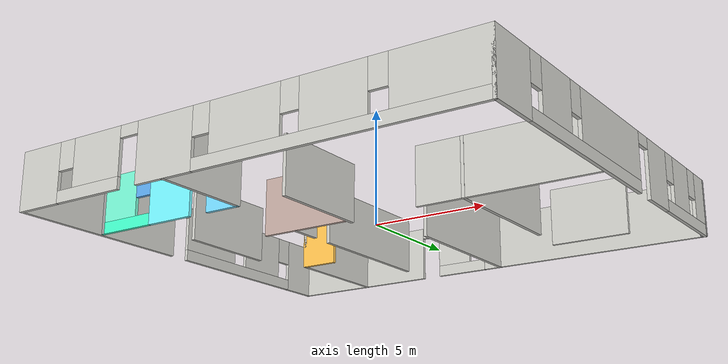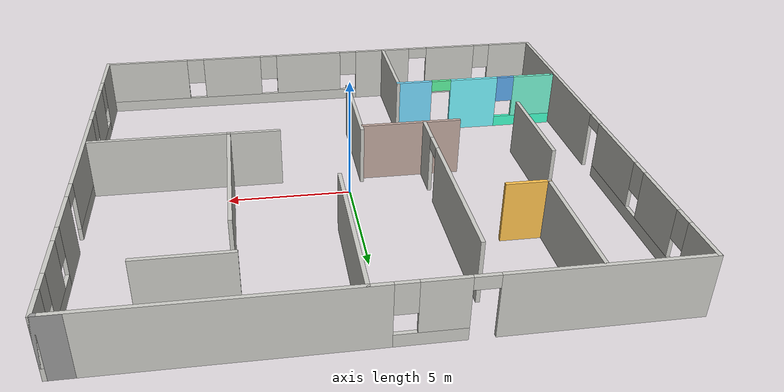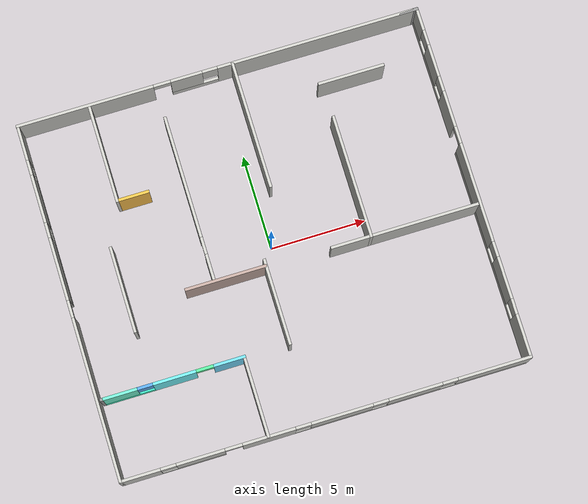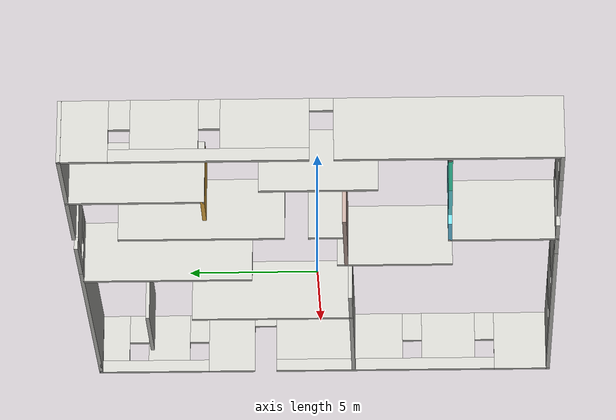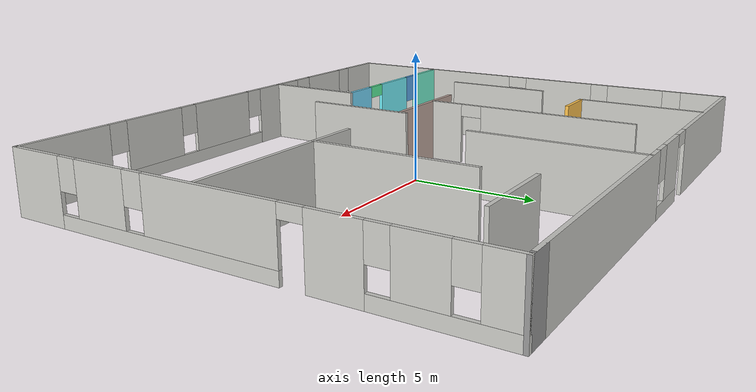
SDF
<?xml version='1.0'?>
<sdf version='1.7'>
  <model name='training_area'>
    <link name='Wall_11'>
      <pose>-2.97768 -7.23047 0 0 0 -1.5708</pose>
      <self_collide>0</self_collide>
      <kinematic>0</kinematic>
      <enable_wind>0</enable_wind>
      <visual name='Wall_11_Visual'>
        <pose>0 0 1.25 0 -0 0</pose>
        <geometry>
          <box>
            <size>4.25 0.15 2.5</size>
          </box>
        </geometry>
        <material>
          <script>
            <uri>file://media/materials/scripts/gazebo.material</uri>
            <name>Gazebo/CeilingTiled</name>
          </script>
          <ambient>0.760784 0.662745 0.627451 1</ambient>
          <shader type='pixel'/>
        </material>
        <meta>
          <layer>0</layer>
        </meta>
        <transparency>0</transparency>
        <cast_shadows>1</cast_shadows>
      </visual>
      <collision name='Wall_11_Collision'>
        <laser_retro>0</laser_retro>
        <max_contacts>10</max_contacts>
        <pose>0 0 1.25 0 -0 0</pose>
        <geometry>
          <box>
            <size>4.25 0.15 2.5</size>
          </box>
        </geometry>
        <surface>
          <friction>
            <ode>
              <mu>1</mu>
              <mu2>1</mu2>
              <fdir1>0 0 0</fdir1>
              <slip1>0</slip1>
              <slip2>0</slip2>
            </ode>
            <torsional>
              <coefficient>1</coefficient>
              <patch_radius>0</patch_radius>
              <surface_radius>0</surface_radius>
              <use_patch_radius>1</use_patch_radius>
              <ode>
                <slip>0</slip>
              </ode>
            </torsional>
          </friction>
          <bounce>
            <restitution_coefficient>0</restitution_coefficient>
            <threshold>1e+06</threshold>
          </bounce>
          <contact>
            <collide_without_contact>0</collide_without_contact>
            <collide_without_contact_bitmask>1</collide_without_contact_bitmask>
            <collide_bitmask>1</collide_bitmask>
            <ode>
              <soft_cfm>0</soft_cfm>
              <soft_erp>0.2</soft_erp>
              <kp>1e+13</kp>
              <kd>1</kd>
              <max_vel>0.01</max_vel>
              <min_depth>0</min_depth>
            </ode>
            <bullet>
              <split_impulse>1</split_impulse>
              <split_impulse_penetration_threshold>-0.01</split_impulse_penetration_threshold>
              <soft_cfm>0</soft_cfm>
              <soft_erp>0.2</soft_erp>
              <kp>1e+13</kp>
              <kd>1</kd>
            </bullet>
          </contact>
        </surface>
      </collision>
    </link>
    <link name='Wall_13'>
      <pose>-6.65268 -5.18047 0 0 -0 3.14159</pose>
      <self_collide>0</self_collide>
      <kinematic>0</kinematic>
      <enable_wind>0</enable_wind>
      <gravity>1</gravity>
      <inertial>
        <mass>1</mass>
        <pose>0 0 0 0 -0 0</pose>
        <inertia>
          <ixx>1</ixx>
          <ixy>0</ixy>
          <ixz>0</ixz>
          <iyy>1</iyy>
          <iyz>0</iyz>
          <izz>1</izz>
        </inertia>
      </inertial>
      <visual name='Wall_13_Visual_2'>
        <pose>2.39091 0 0.25 0 -0 0</pose>
        <geometry>
          <box>
            <size>2.71819 0.15 0.5</size>
          </box>
        </geometry>
        <material>
          <script>
            <uri>file://media/materials/scripts/gazebo.material</uri>
            <name>Gazebo/Grey</name>
          </script>
          <ambient>0.261 1 0.8 1</ambient>
          <shader type='pixel'>
            <normal_map>__default__</normal_map>
          </shader>
          <diffuse>0.7 0.7 0.7 1</diffuse>
          <specular>0.01 0.01 0.01 1</specular>
          <emissive>0 0 0 1</emissive>
        </material>
        <meta>
          <layer>0</layer>
        </meta>
        <transparency>0</transparency>
        <cast_shadows>1</cast_shadows>
      </visual>
      <visual name='Wall_13_Visual_5'>
        <pose>-1.64458 0 2.25 0 -0 0</pose>
        <geometry>
          <box>
            <size>0.9 0.15 0.5</size>
          </box>
        </geometry>
        <material>
          <script>
            <uri>file://media/materials/scripts/gazebo.material</uri>
            <name>Gazebo/Grey</name>
          </script>
          <ambient>0.361 0.963 0.627 1</ambient>
          <shader type='pixel'>
            <normal_map>__default__</normal_map>
          </shader>
          <diffuse>0.7 0.7 0.7 1</diffuse>
          <specular>0.01 0.01 0.01 1</specular>
          <emissive>0 0 0 1</emissive>
        </material>
        <meta>
          <layer>0</layer>
        </meta>
        <transparency>0</transparency>
        <cast_shadows>1</cast_shadows>
      </visual>
      <visual name='Wall_13_Visual_3'>
        <pose>2.79091 0 1.5 0 -0 0</pose>
        <geometry>
          <box>
            <size>1.91819 0.15 2</size>
          </box>
        </geometry>
        <material>
          <script>
            <uri>file://media/materials/scripts/gazebo.material</uri>
            <name>Gazebo/Grey</name>
          </script>
          <ambient>0.461 0.963 0.827 1</ambient>
          <shader type='pixel'>
            <normal_map>__default__</normal_map>
          </shader>
          <diffuse>0.7 0.7 0.7 1</diffuse>
          <specular>0.01 0.01 0.01 1</specular>
          <emissive>0 0 0 1</emissive>
        </material>
        <meta>
          <layer>0</layer>
        </meta>
        <transparency>0</transparency>
        <cast_shadows>1</cast_shadows>
      </visual>
      <visual name='Wall_13_Visual_1'>
        <pose>-0.081383 0 1.25 0 -0 0</pose>
        <geometry>
          <box>
            <size>2.22639 0.15 2.5</size>
          </box>
        </geometry>
        <material>
          <script>
            <uri>file://media/materials/scripts/gazebo.material</uri>
            <name>Gazebo/Grey</name>
          </script>
          <ambient>0.461 0.963 1 1</ambient>
          <shader type='pixel'>
            <normal_map>__default__</normal_map>
          </shader>
          <diffuse>0.7 0.7 0.7 1</diffuse>
          <specular>0.01 0.01 0.01 1</specular>
          <emissive>0 0 0 1</emissive>
        </material>
        <meta>
          <layer>0</layer>
        </meta>
        <transparency>0</transparency>
        <cast_shadows>1</cast_shadows>
      </visual>
      <visual name='Wall_13_Visual_4'>
        <pose>1.43181 0 1.9 0 -0 0</pose>
        <geometry>
          <box>
            <size>0.8 0.15 1.2</size>
          </box>
        </geometry>
        <material>
          <script>
            <uri>file://media/materials/scripts/gazebo.material</uri>
            <name>Gazebo/Grey</name>
          </script>
          <ambient>0.361 0.663 0.927 1</ambient>
          <shader type='pixel'>
            <normal_map>__default__</normal_map>
          </shader>
          <diffuse>0.7 0.7 0.7 1</diffuse>
          <specular>0.01 0.01 0.01 1</specular>
          <emissive>0 0 0 1</emissive>
        </material>
        <meta>
          <layer>0</layer>
        </meta>
        <transparency>0</transparency>
        <cast_shadows>1</cast_shadows>
      </visual>
      <visual name='Wall_13_Visual_0'>
        <pose>-2.92229 0 1.25 0 -0 0</pose>
        <geometry>
          <box>
            <size>1.65542 0.15 2.5</size>
          </box>
        </geometry>
        <material>
          <script>
            <uri>file://media/materials/scripts/gazebo.material</uri>
            <name>Gazebo/Grey</name>
          </script>
          <ambient>0.461 0.863 1 1</ambient>
          <shader type='pixel'>
            <normal_map>__default__</normal_map>
          </shader>
          <diffuse>0.7 0.7 0.7 1</diffuse>
          <specular>0.01 0.01 0.01 1</specular>
          <emissive>0 0 0 1</emissive>
        </material>
        <meta>
          <layer>0</layer>
        </meta>
        <transparency>0</transparency>
        <cast_shadows>1</cast_shadows>
      </visual>
      <collision name='Wall_13_Collision_4'>
        <laser_retro>0</laser_retro>
        <max_contacts>10</max_contacts>
        <pose>1.43181 0 1.9 0 -0 0</pose>
        <geometry>
          <box>
            <size>0.8 0.15 1.2</size>
          </box>
        </geometry>
        <surface>
          <friction>
            <ode>
              <mu>1</mu>
              <mu2>1</mu2>
              <fdir1>0 0 0</fdir1>
              <slip1>0</slip1>
              <slip2>0</slip2>
            </ode>
            <torsional>
              <coefficient>1</coefficient>
              <patch_radius>0</patch_radius>
              <surface_radius>0</surface_radius>
              <use_patch_radius>1</use_patch_radius>
              <ode>
                <slip>0</slip>
              </ode>
            </torsional>
          </friction>
          <bounce>
            <restitution_coefficient>0</restitution_coefficient>
            <threshold>1e+06</threshold>
          </bounce>
          <contact>
            <collide_without_contact>0</collide_without_contact>
            <collide_without_contact_bitmask>1</collide_without_contact_bitmask>
            <collide_bitmask>1</collide_bitmask>
            <ode>
              <soft_cfm>0</soft_cfm>
              <soft_erp>0.2</soft_erp>
              <kp>1e+13</kp>
              <kd>1</kd>
              <max_vel>0.01</max_vel>
              <min_depth>0</min_depth>
            </ode>
            <bullet>
              <split_impulse>1</split_impulse>
              <split_impulse_penetration_threshold>-0.01</split_impulse_penetration_threshold>
              <soft_cfm>0</soft_cfm>
              <soft_erp>0.2</soft_erp>
              <kp>1e+13</kp>
              <kd>1</kd>
            </bullet>
          </contact>
        </surface>
      </collision>
      <collision name='Wall_13_Collision_1'>
        <laser_retro>0</laser_retro>
        <max_contacts>10</max_contacts>
        <pose>-0.081383 0 1.25 0 -0 0</pose>
        <geometry>
          <box>
            <size>2.22639 0.15 2.5</size>
          </box>
        </geometry>
        <surface>
          <friction>
            <ode>
              <mu>1</mu>
              <mu2>1</mu2>
              <fdir1>0 0 0</fdir1>
              <slip1>0</slip1>
              <slip2>0</slip2>
            </ode>
            <torsional>
              <coefficient>1</coefficient>
              <patch_radius>0</patch_radius>
              <surface_radius>0</surface_radius>
              <use_patch_radius>1</use_patch_radius>
              <ode>
                <slip>0</slip>
              </ode>
            </torsional>
          </friction>
          <bounce>
            <restitution_coefficient>0</restitution_coefficient>
            <threshold>1e+06</threshold>
          </bounce>
          <contact>
            <collide_without_contact>0</collide_without_contact>
            <collide_without_contact_bitmask>1</collide_without_contact_bitmask>
            <collide_bitmask>1</collide_bitmask>
            <ode>
              <soft_cfm>0</soft_cfm>
              <soft_erp>0.2</soft_erp>
              <kp>1e+13</kp>
              <kd>1</kd>
              <max_vel>0.01</max_vel>
              <min_depth>0</min_depth>
            </ode>
            <bullet>
              <split_impulse>1</split_impulse>
              <split_impulse_penetration_threshold>-0.01</split_impulse_penetration_threshold>
              <soft_cfm>0</soft_cfm>
              <soft_erp>0.2</soft_erp>
              <kp>1e+13</kp>
              <kd>1</kd>
            </bullet>
          </contact>
        </surface>
      </collision>
      <collision name='Wall_13_Collision_2'>
        <laser_retro>0</laser_retro>
        <max_contacts>10</max_contacts>
        <pose>2.39091 0 0.25 0 -0 0</pose>
        <geometry>
          <box>
            <size>2.71819 0.15 0.5</size>
          </box>
        </geometry>
        <surface>
          <friction>
            <ode>
              <mu>1</mu>
              <mu2>1</mu2>
              <fdir1>0 0 0</fdir1>
              <slip1>0</slip1>
              <slip2>0</slip2>
            </ode>
            <torsional>
              <coefficient>1</coefficient>
              <patch_radius>0</patch_radius>
              <surface_radius>0</surface_radius>
              <use_patch_radius>1</use_patch_radius>
              <ode>
                <slip>0</slip>
              </ode>
            </torsional>
          </friction>
          <bounce>
            <restitution_coefficient>0</restitution_coefficient>
            <threshold>1e+06</threshold>
          </bounce>
          <contact>
            <collide_without_contact>0</collide_without_contact>
            <collide_without_contact_bitmask>1</collide_without_contact_bitmask>
            <collide_bitmask>1</collide_bitmask>
            <ode>
              <soft_cfm>0</soft_cfm>
              <soft_erp>0.2</soft_erp>
              <kp>1e+13</kp>
              <kd>1</kd>
              <max_vel>0.01</max_vel>
              <min_depth>0</min_depth>
            </ode>
            <bullet>
              <split_impulse>1</split_impulse>
              <split_impulse_penetration_threshold>-0.01</split_impulse_penetration_threshold>
              <soft_cfm>0</soft_cfm>
              <soft_erp>0.2</soft_erp>
              <kp>1e+13</kp>
              <kd>1</kd>
            </bullet>
          </contact>
        </surface>
      </collision>
      <collision name='Wall_13_Collision_0'>
        <laser_retro>0</laser_retro>
        <max_contacts>10</max_contacts>
        <pose>-2.92229 0 1.25 0 -0 0</pose>
        <geometry>
          <box>
            <size>1.65542 0.15 2.5</size>
          </box>
        </geometry>
        <surface>
          <friction>
            <ode>
              <mu>1</mu>
              <mu2>1</mu2>
              <fdir1>0 0 0</fdir1>
              <slip1>0</slip1>
              <slip2>0</slip2>
            </ode>
            <torsional>
              <coefficient>1</coefficient>
              <patch_radius>0</patch_radius>
              <surface_radius>0</surface_radius>
              <use_patch_radius>1</use_patch_radius>
              <ode>
                <slip>0</slip>
              </ode>
            </torsional>
          </friction>
          <bounce>
            <restitution_coefficient>0</restitution_coefficient>
            <threshold>1e+06</threshold>
          </bounce>
          <contact>
            <collide_without_contact>0</collide_without_contact>
            <collide_without_contact_bitmask>1</collide_without_contact_bitmask>
            <collide_bitmask>1</collide_bitmask>
            <ode>
              <soft_cfm>0</soft_cfm>
              <soft_erp>0.2</soft_erp>
              <kp>1e+13</kp>
              <kd>1</kd>
              <max_vel>0.01</max_vel>
              <min_depth>0</min_depth>
            </ode>
            <bullet>
              <split_impulse>1</split_impulse>
              <split_impulse_penetration_threshold>-0.01</split_impulse_penetration_threshold>
              <soft_cfm>0</soft_cfm>
              <soft_erp>0.2</soft_erp>
              <kp>1e+13</kp>
              <kd>1</kd>
            </bullet>
          </contact>
        </surface>
      </collision>
      <collision name='Wall_13_Collision_5'>
        <laser_retro>0</laser_retro>
        <max_contacts>10</max_contacts>
        <pose>-1.64458 0 2.25 0 -0 0</pose>
        <geometry>
          <box>
            <size>0.9 0.15 0.5</size>
          </box>
        </geometry>
        <surface>
          <friction>
            <ode>
              <mu>1</mu>
              <mu2>1</mu2>
              <fdir1>0 0 0</fdir1>
              <slip1>0</slip1>
              <slip2>0</slip2>
            </ode>
            <torsional>
              <coefficient>1</coefficient>
              <patch_radius>0</patch_radius>
              <surface_radius>0</surface_radius>
              <use_patch_radius>1</use_patch_radius>
              <ode>
                <slip>0</slip>
              </ode>
            </torsional>
          </friction>
          <bounce>
            <restitution_coefficient>0</restitution_coefficient>
            <threshold>1e+06</threshold>
          </bounce>
          <contact>
            <collide_without_contact>0</collide_without_contact>
            <collide_without_contact_bitmask>1</collide_without_contact_bitmask>
            <collide_bitmask>1</collide_bitmask>
            <ode>
              <soft_cfm>0</soft_cfm>
              <soft_erp>0.2</soft_erp>
              <kp>1e+13</kp>
              <kd>1</kd>
              <max_vel>0.01</max_vel>
              <min_depth>0</min_depth>
            </ode>
            <bullet>
              <split_impulse>1</split_impulse>
              <split_impulse_penetration_threshold>-0.01</split_impulse_penetration_threshold>
              <soft_cfm>0</soft_cfm>
              <soft_erp>0.2</soft_erp>
              <kp>1e+13</kp>
              <kd>1</kd>
            </bullet>
          </contact>
        </surface>
      </collision>
      <collision name='Wall_13_Collision_3'>
        <laser_retro>0</laser_retro>
        <max_contacts>10</max_contacts>
        <pose>2.79091 0 1.5 0 -0 0</pose>
        <geometry>
          <box>
            <size>1.91819 0.15 2</size>
          </box>
        </geometry>
        <surface>
          <friction>
            <ode>
              <mu>1</mu>
              <mu2>1</mu2>
              <fdir1>0 0 0</fdir1>
              <slip1>0</slip1>
              <slip2>0</slip2>
            </ode>
            <torsional>
              <coefficient>1</coefficient>
              <patch_radius>0</patch_radius>
              <surface_radius>0</surface_radius>
              <use_patch_radius>1</use_patch_radius>
              <ode>
                <slip>0</slip>
              </ode>
            </torsional>
          </friction>
          <bounce>
            <restitution_coefficient>0</restitution_coefficient>
            <threshold>1e+06</threshold>
          </bounce>
          <contact>
            <collide_without_contact>0</collide_without_contact>
            <collide_without_contact_bitmask>1</collide_without_contact_bitmask>
            <collide_bitmask>1</collide_bitmask>
            <ode>
              <soft_cfm>0</soft_cfm>
              <soft_erp>0.2</soft_erp>
              <kp>1e+13</kp>
              <kd>1</kd>
              <max_vel>0.01</max_vel>
              <min_depth>0</min_depth>
            </ode>
            <bullet>
              <split_impulse>1</split_impulse>
              <split_impulse_penetration_threshold>-0.01</split_impulse_penetration_threshold>
              <soft_cfm>0</soft_cfm>
              <soft_erp>0.2</soft_erp>
              <kp>1e+13</kp>
              <kd>1</kd>
            </bullet>
          </contact>
        </surface>
      </collision>
    </link>
    <link name='Wall_14'>
      <pose>-10.3277 -5.18047 0 0 -0 0</pose>
      <self_collide>0</self_collide>
      <kinematic>0</kinematic>
      <enable_wind>0</enable_wind>
      <visual name='Wall_14_Visual'>
        <pose>0 0 1.25 0 -0 0</pose>
        <geometry>
          <box>
            <size>0.15 0.15 2.5</size>
          </box>
        </geometry>
        <material>
          <script>
            <uri>file://media/materials/scripts/gazebo.material</uri>
            <name>Gazebo/Grey</name>
          </script>
          <ambient>1 1 1 1</ambient>
          <shader type='pixel'/>
        </material>
        <meta>
          <layer>0</layer>
        </meta>
        <transparency>0</transparency>
        <cast_shadows>1</cast_shadows>
      </visual>
      <collision name='Wall_14_Collision'>
        <laser_retro>0</laser_retro>
        <max_contacts>10</max_contacts>
        <pose>0 0 1.25 0 -0 0</pose>
        <geometry>
          <box>
            <size>0.15 0.15 2.5</size>
          </box>
        </geometry>
        <surface>
          <friction>
            <ode>
              <mu>1</mu>
              <mu2>1</mu2>
              <fdir1>0 0 0</fdir1>
              <slip1>0</slip1>
              <slip2>0</slip2>
            </ode>
            <torsional>
              <coefficient>1</coefficient>
              <patch_radius>0</patch_radius>
              <surface_radius>0</surface_radius>
              <use_patch_radius>1</use_patch_radius>
              <ode>
                <slip>0</slip>
              </ode>
            </torsional>
          </friction>
          <bounce>
            <restitution_coefficient>0</restitution_coefficient>
            <threshold>1e+06</threshold>
          </bounce>
          <contact>
            <collide_without_contact>0</collide_without_contact>
            <collide_without_contact_bitmask>1</collide_without_contact_bitmask>
            <collide_bitmask>1</collide_bitmask>
            <ode>
              <soft_cfm>0</soft_cfm>
              <soft_erp>0.2</soft_erp>
              <kp>1e+13</kp>
              <kd>1</kd>
              <max_vel>0.01</max_vel>
              <min_depth>0</min_depth>
            </ode>
            <bullet>
              <split_impulse>1</split_impulse>
              <split_impulse_penetration_threshold>-0.01</split_impulse_penetration_threshold>
              <soft_cfm>0</soft_cfm>
              <soft_erp>0.2</soft_erp>
              <kp>1e+13</kp>
              <kd>1</kd>
            </bullet>
          </contact>
        </surface>
      </collision>
    </link>
    <link name='Wall_16'>
      <pose>-2.72495 -1.14348 0 0 -0 0</pose>
      <self_collide>0</self_collide>
      <kinematic>0</kinematic>
      <enable_wind>0</enable_wind>
      <visual name='Wall_16_Visual'>
        <pose>0 0 1.25 0 -0 0</pose>
        <geometry>
          <box>
            <size>4.25 0.15 2.5</size>
          </box>
        </geometry>
        <material>
          <script>
            <uri>file://media/materials/scripts/gazebo.material</uri>
            <name>Gazebo/Grey</name>
          </script>
          <ambient>0.760784 0.662745 0.627451 1</ambient>
          <shader type='pixel'/>
        </material>
        <meta>
          <layer>0</layer>
        </meta>
        <transparency>0</transparency>
        <cast_shadows>1</cast_shadows>
      </visual>
      <collision name='Wall_16_Collision'>
        <laser_retro>0</laser_retro>
        <max_contacts>10</max_contacts>
        <pose>0 0 1.25 0 -0 0</pose>
        <geometry>
          <box>
            <size>4.25 0.15 2.5</size>
          </box>
        </geometry>
        <surface>
          <friction>
            <ode>
              <mu>1</mu>
              <mu2>1</mu2>
              <fdir1>0 0 0</fdir1>
              <slip1>0</slip1>
              <slip2>0</slip2>
            </ode>
            <torsional>
              <coefficient>1</coefficient>
              <patch_radius>0</patch_radius>
              <surface_radius>0</surface_radius>
              <use_patch_radius>1</use_patch_radius>
              <ode>
                <slip>0</slip>
              </ode>
            </torsional>
          </friction>
          <bounce>
            <restitution_coefficient>0</restitution_coefficient>
            <threshold>1e+06</threshold>
          </bounce>
          <contact>
            <collide_without_contact>0</collide_without_contact>
            <collide_without_contact_bitmask>1</collide_without_contact_bitmask>
            <collide_bitmask>1</collide_bitmask>
            <ode>
              <soft_cfm>0</soft_cfm>
              <soft_erp>0.2</soft_erp>
              <kp>1e+13</kp>
              <kd>1</kd>
              <max_vel>0.01</max_vel>
              <min_depth>0</min_depth>
            </ode>
            <bullet>
              <split_impulse>1</split_impulse>
              <split_impulse_penetration_threshold>-0.01</split_impulse_penetration_threshold>
              <soft_cfm>0</soft_cfm>
              <soft_erp>0.2</soft_erp>
              <kp>1e+13</kp>
              <kd>1</kd>
            </bullet>
          </contact>
        </surface>
      </collision>
    </link>
    <link name='Wall_18'>
      <pose>-3.31028 3.23789 0 0 -0 1.5708</pose>
      <self_collide>0</self_collide>
      <kinematic>0</kinematic>
      <enable_wind>0</enable_wind>
      <gravity>1</gravity>
      <inertial>
        <mass>1</mass>
        <pose>0 0 0 0 -0 0</pose>
        <inertia>
          <ixx>1</ixx>
          <ixy>0</ixy>
          <ixz>0</ixz>
          <iyy>1</iyy>
          <iyz>0</iyz>
          <izz>1</izz>
        </inertia>
      </inertial>
      <visual name='Wall_18_Visual_1'>
        <pose>1.15758 0 1.25 0 -0 0</pose>
        <geometry>
          <box>
            <size>6.43485 0.15 2.5</size>
          </box>
        </geometry>
        <material>
          <script>
            <uri>file://media/materials/scripts/gazebo.material</uri>
            <name>Gazebo/CeilingTiled</name>
          </script>
          <ambient>0.361 0.363 0.927 1</ambient>
          <shader type='pixel'>
            <normal_map>__default__</normal_map>
          </shader>
          <diffuse>1 1 1 1</diffuse>
          <specular>0 0 0 1</specular>
          <emissive>0 0 0 1</emissive>
        </material>
        <meta>
          <layer>0</layer>
        </meta>
        <transparency>0</transparency>
        <cast_shadows>1</cast_shadows>
      </visual>
      <visual name='Wall_18_Visual_2'>
        <pose>-2.50985 0 2.25 0 -0 0</pose>
        <geometry>
          <box>
            <size>0.9 0.15 0.5</size>
          </box>
        </geometry>
        <material>
          <script>
            <uri>file://media/materials/scripts/gazebo.material</uri>
            <name>Gazebo/CeilingTiled</name>
          </script>
          <ambient>0.361 0.363 0.627 1</ambient>
          <shader type='pixel'>
            <normal_map>__default__</normal_map>
          </shader>
          <diffuse>1 1 1 1</diffuse>
          <specular>0 0 0 1</specular>
          <emissive>0 0 0 1</emissive>
        </material>
        <meta>
          <layer>0</layer>
        </meta>
        <transparency>0</transparency>
        <cast_shadows>1</cast_shadows>
      </visual>
      <visual name='Wall_18_Visual_0'>
        <pose>-3.66742 0 1.25 0 -0 0</pose>
        <geometry>
          <box>
            <size>1.41515 0.15 2.5</size>
          </box>
        </geometry>
        <material>
          <script>
            <uri>file://media/materials/scripts/gazebo.material</uri>
            <name>Gazebo/CeilingTiled</name>
          </script>
          <ambient>0.961 0.363 0.327 1</ambient>
          <shader type='pixel'>
            <normal_map>__default__</normal_map>
          </shader>
          <diffuse>1 1 1 1</diffuse>
          <specular>0 0 0 1</specular>
          <emissive>0 0 0 1</emissive>
        </material>
        <meta>
          <layer>0</layer>
        </meta>
        <transparency>0</transparency>
        <cast_shadows>1</cast_shadows>
      </visual>
      <collision name='Wall_18_Collision_0'>
        <laser_retro>0</laser_retro>
        <max_contacts>10</max_contacts>
        <pose>-3.66742 0 1.25 0 -0 0</pose>
        <geometry>
          <box>
            <size>1.41515 0.15 2.5</size>
          </box>
        </geometry>
        <surface>
          <friction>
            <ode>
              <mu>1</mu>
              <mu2>1</mu2>
              <fdir1>0 0 0</fdir1>
              <slip1>0</slip1>
              <slip2>0</slip2>
            </ode>
            <torsional>
              <coefficient>1</coefficient>
              <patch_radius>0</patch_radius>
              <surface_radius>0</surface_radius>
              <use_patch_radius>1</use_patch_radius>
              <ode>
                <slip>0</slip>
              </ode>
            </torsional>
          </friction>
          <bounce>
            <restitution_coefficient>0</restitution_coefficient>
            <threshold>1e+06</threshold>
          </bounce>
          <contact>
            <collide_without_contact>0</collide_without_contact>
            <collide_without_contact_bitmask>1</collide_without_contact_bitmask>
            <collide_bitmask>1</collide_bitmask>
            <ode>
              <soft_cfm>0</soft_cfm>
              <soft_erp>0.2</soft_erp>
              <kp>1e+13</kp>
              <kd>1</kd>
              <max_vel>0.01</max_vel>
              <min_depth>0</min_depth>
            </ode>
            <bullet>
              <split_impulse>1</split_impulse>
              <split_impulse_penetration_threshold>-0.01</split_impulse_penetration_threshold>
              <soft_cfm>0</soft_cfm>
              <soft_erp>0.2</soft_erp>
              <kp>1e+13</kp>
              <kd>1</kd>
            </bullet>
          </contact>
        </surface>
      </collision>
      <collision name='Wall_18_Collision_2'>
        <laser_retro>0</laser_retro>
        <max_contacts>10</max_contacts>
        <pose>-2.50985 0 2.25 0 -0 0</pose>
        <geometry>
          <box>
            <size>0.9 0.15 0.5</size>
          </box>
        </geometry>
        <surface>
          <friction>
            <ode>
              <mu>1</mu>
              <mu2>1</mu2>
              <fdir1>0 0 0</fdir1>
              <slip1>0</slip1>
              <slip2>0</slip2>
            </ode>
            <torsional>
              <coefficient>1</coefficient>
              <patch_radius>0</patch_radius>
              <surface_radius>0</surface_radius>
              <use_patch_radius>1</use_patch_radius>
              <ode>
                <slip>0</slip>
              </ode>
            </torsional>
          </friction>
          <bounce>
            <restitution_coefficient>0</restitution_coefficient>
            <threshold>1e+06</threshold>
          </bounce>
          <contact>
            <collide_without_contact>0</collide_without_contact>
            <collide_without_contact_bitmask>1</collide_without_contact_bitmask>
            <collide_bitmask>1</collide_bitmask>
            <ode>
              <soft_cfm>0</soft_cfm>
              <soft_erp>0.2</soft_erp>
              <kp>1e+13</kp>
              <kd>1</kd>
              <max_vel>0.01</max_vel>
              <min_depth>0</min_depth>
            </ode>
            <bullet>
              <split_impulse>1</split_impulse>
              <split_impulse_penetration_threshold>-0.01</split_impulse_penetration_threshold>
              <soft_cfm>0</soft_cfm>
              <soft_erp>0.2</soft_erp>
              <kp>1e+13</kp>
              <kd>1</kd>
            </bullet>
          </contact>
        </surface>
      </collision>
      <collision name='Wall_18_Collision_1'>
        <laser_retro>0</laser_retro>
        <max_contacts>10</max_contacts>
        <pose>1.15758 0 1.25 0 -0 0</pose>
        <geometry>
          <box>
            <size>6.43485 0.15 2.5</size>
          </box>
        </geometry>
        <surface>
          <friction>
            <ode>
              <mu>1</mu>
              <mu2>1</mu2>
              <fdir1>0 0 0</fdir1>
              <slip1>0</slip1>
              <slip2>0</slip2>
            </ode>
            <torsional>
              <coefficient>1</coefficient>
              <patch_radius>0</patch_radius>
              <surface_radius>0</surface_radius>
              <use_patch_radius>1</use_patch_radius>
              <ode>
                <slip>0</slip>
              </ode>
            </torsional>
          </friction>
          <bounce>
            <restitution_coefficient>0</restitution_coefficient>
            <threshold>1e+06</threshold>
          </bounce>
          <contact>
            <collide_without_contact>0</collide_without_contact>
            <collide_without_contact_bitmask>1</collide_without_contact_bitmask>
            <collide_bitmask>1</collide_bitmask>
            <ode>
              <soft_cfm>0</soft_cfm>
              <soft_erp>0.2</soft_erp>
              <kp>1e+13</kp>
              <kd>1</kd>
              <max_vel>0.01</max_vel>
              <min_depth>0</min_depth>
            </ode>
            <bullet>
              <split_impulse>1</split_impulse>
              <split_impulse_penetration_threshold>-0.01</split_impulse_penetration_threshold>
              <soft_cfm>0</soft_cfm>
              <soft_erp>0.2</soft_erp>
              <kp>1e+13</kp>
              <kd>1</kd>
            </bullet>
          </contact>
        </surface>
      </collision>
    </link>
    <link name='Wall_20'>
      <pose>-0.625048 -3.03701 0 0 -0 1.5708</pose>
      <self_collide>0</self_collide>
      <kinematic>0</kinematic>
      <enable_wind>0</enable_wind>
      <gravity>1</gravity>
      <inertial>
        <mass>1</mass>
        <pose>0 0 0 0 -0 0</pose>
        <inertia>
          <ixx>1</ixx>
          <ixy>0</ixy>
          <ixz>0</ixz>
          <iyy>1</iyy>
          <iyz>0</iyz>
          <izz>1</izz>
        </inertia>
      </inertial>
      <visual name='Wall_20_Visual'>
        <pose>0 0 1.25 0 -0 0</pose>
        <geometry>
          <box>
            <size>4.5 0.15 2.5</size>
          </box>
        </geometry>
        <material>
          <script>
            <uri>file://media/materials/scripts/gazebo.material</uri>
            <name>Gazebo/CeilingTiled</name>
          </script>
          <ambient>0.596 0.475 0.42 1</ambient>
          <shader type='pixel'>
            <normal_map>__default__</normal_map>
          </shader>
          <diffuse>1 1 1 1</diffuse>
          <specular>0 0 0 1</specular>
          <emissive>0 0 0 1</emissive>
        </material>
        <meta>
          <layer>0</layer>
        </meta>
        <transparency>0</transparency>
        <cast_shadows>1</cast_shadows>
      </visual>
      <collision name='Wall_20_Collision'>
        <laser_retro>0</laser_retro>
        <max_contacts>10</max_contacts>
        <pose>0 0 1.25 0 -0 0</pose>
        <geometry>
          <box>
            <size>4.5 0.15 2.5</size>
          </box>
        </geometry>
        <surface>
          <friction>
            <ode>
              <mu>1</mu>
              <mu2>1</mu2>
              <fdir1>0 0 0</fdir1>
              <slip1>0</slip1>
              <slip2>0</slip2>
            </ode>
            <torsional>
              <coefficient>1</coefficient>
              <patch_radius>0</patch_radius>
              <surface_radius>0</surface_radius>
              <use_patch_radius>1</use_patch_radius>
              <ode>
                <slip>0</slip>
              </ode>
            </torsional>
          </friction>
          <bounce>
            <restitution_coefficient>0</restitution_coefficient>
            <threshold>1e+06</threshold>
          </bounce>
          <contact>
            <collide_without_contact>0</collide_without_contact>
            <collide_without_contact_bitmask>1</collide_without_contact_bitmask>
            <collide_bitmask>1</collide_bitmask>
            <ode>
              <soft_cfm>0</soft_cfm>
              <soft_erp>0.2</soft_erp>
              <kp>1e+13</kp>
              <kd>1</kd>
              <max_vel>0.01</max_vel>
              <min_depth>0</min_depth>
            </ode>
            <bullet>
              <split_impulse>1</split_impulse>
              <split_impulse_penetration_threshold>-0.01</split_impulse_penetration_threshold>
              <soft_cfm>0</soft_cfm>
              <soft_erp>0.2</soft_erp>
              <kp>1e+13</kp>
              <kd>1</kd>
            </bullet>
          </contact>
        </surface>
      </collision>
    </link>
    <link name='Wall_22'>
      <pose>-6.80922 6.72196 0 0 0 -1.5708</pose>
      <self_collide>0</self_collide>
      <kinematic>0</kinematic>
      <enable_wind>0</enable_wind>
      <visual name='Wall_22_Visual'>
        <pose>0 0 1.25 0 -0 0</pose>
        <geometry>
          <box>
            <size>5.25 0.15 2.5</size>
          </box>
        </geometry>
        <material>
          <script>
            <uri>file://media/materials/scripts/gazebo.material</uri>
            <name>Gazebo/CeilingTiled</name>
          </script>
          <ambient>1 0.764706 0.305882 1</ambient>
          <shader type='pixel'/>
        </material>
        <meta>
          <layer>0</layer>
        </meta>
        <transparency>0</transparency>
        <cast_shadows>1</cast_shadows>
      </visual>
      <collision name='Wall_22_Collision'>
        <laser_retro>0</laser_retro>
        <max_contacts>10</max_contacts>
        <pose>0 0 1.25 0 -0 0</pose>
        <geometry>
          <box>
            <size>5.25 0.15 2.5</size>
          </box>
        </geometry>
        <surface>
          <friction>
            <ode>
              <mu>1</mu>
              <mu2>1</mu2>
              <fdir1>0 0 0</fdir1>
              <slip1>0</slip1>
              <slip2>0</slip2>
            </ode>
            <torsional>
              <coefficient>1</coefficient>
              <patch_radius>0</patch_radius>
              <surface_radius>0</surface_radius>
              <use_patch_radius>1</use_patch_radius>
              <ode>
                <slip>0</slip>
              </ode>
            </torsional>
          </friction>
          <bounce>
            <restitution_coefficient>0</restitution_coefficient>
            <threshold>1e+06</threshold>
          </bounce>
          <contact>
            <collide_without_contact>0</collide_without_contact>
            <collide_without_contact_bitmask>1</collide_without_contact_bitmask>
            <collide_bitmask>1</collide_bitmask>
            <ode>
              <soft_cfm>0</soft_cfm>
              <soft_erp>0.2</soft_erp>
              <kp>1e+13</kp>
              <kd>1</kd>
              <max_vel>0.01</max_vel>
              <min_depth>0</min_depth>
            </ode>
            <bullet>
              <split_impulse>1</split_impulse>
              <split_impulse_penetration_threshold>-0.01</split_impulse_penetration_threshold>
              <soft_cfm>0</soft_cfm>
              <soft_erp>0.2</soft_erp>
              <kp>1e+13</kp>
              <kd>1</kd>
            </bullet>
          </contact>
        </surface>
      </collision>
    </link>
    <link name='Wall_23'>
      <pose>-6.00922 4.17196 0 0 -0 0</pose>
      <self_collide>0</self_collide>
      <kinematic>0</kinematic>
      <enable_wind>0</enable_wind>
      <visual name='Wall_23_Visual'>
        <pose>0 0 1.25 0 -0 0</pose>
        <geometry>
          <box>
            <size>1.75 0.15 2.5</size>
          </box>
        </geometry>
        <material>
          <script>
            <uri>file://media/materials/scripts/gazebo.material</uri>
            <name>Gazebo/Grey</name>
          </script>
          <ambient>1 0.764706 0.305882 1</ambient>
          <shader type='pixel'/>
        </material>
        <meta>
          <layer>0</layer>
        </meta>
        <transparency>0</transparency>
        <cast_shadows>1</cast_shadows>
      </visual>
      <collision name='Wall_23_Collision'>
        <laser_retro>0</laser_retro>
        <max_contacts>10</max_contacts>
        <pose>0 0 1.25 0 -0 0</pose>
        <geometry>
          <box>
            <size>1.75 0.15 2.5</size>
          </box>
        </geometry>
        <surface>
          <friction>
            <ode>
              <mu>1</mu>
              <mu2>1</mu2>
              <fdir1>0 0 0</fdir1>
              <slip1>0</slip1>
              <slip2>0</slip2>
            </ode>
            <torsional>
              <coefficient>1</coefficient>
              <patch_radius>0</patch_radius>
              <surface_radius>0</surface_radius>
              <use_patch_radius>1</use_patch_radius>
              <ode>
                <slip>0</slip>
              </ode>
            </torsional>
          </friction>
          <bounce>
            <restitution_coefficient>0</restitution_coefficient>
            <threshold>1e+06</threshold>
          </bounce>
          <contact>
            <collide_without_contact>0</collide_without_contact>
            <collide_without_contact_bitmask>1</collide_without_contact_bitmask>
            <collide_bitmask>1</collide_bitmask>
            <ode>
              <soft_cfm>0</soft_cfm>
              <soft_erp>0.2</soft_erp>
              <kp>1e+13</kp>
              <kd>1</kd>
              <max_vel>0.01</max_vel>
              <min_depth>0</min_depth>
            </ode>
            <bullet>
              <split_impulse>1</split_impulse>
              <split_impulse_penetration_threshold>-0.01</split_impulse_penetration_threshold>
              <soft_cfm>0</soft_cfm>
              <soft_erp>0.2</soft_erp>
              <kp>1e+13</kp>
              <kd>1</kd>
            </bullet>
          </contact>
        </surface>
      </collision>
    </link>
    <link name='Wall_26'>
      <pose>-7.78566 -0.226392 0 0 0 -1.5708</pose>
      <self_collide>0</self_collide>
      <kinematic>0</kinematic>
      <enable_wind>0</enable_wind>
      <gravity>1</gravity>
      <inertial>
        <mass>1</mass>
        <pose>0 0 0 0 -0 0</pose>
        <inertia>
          <ixx>1</ixx>
          <ixy>0</ixy>
          <ixz>0</ixz>
          <iyy>1</iyy>
          <iyz>0</iyz>
          <izz>1</izz>
        </inertia>
      </inertial>
      <visual name='Wall_26_Visual'>
        <pose>0 0 1.25 0 -0 0</pose>
        <geometry>
          <box>
            <size>4.5 0.15 2.5</size>
          </box>
        </geometry>
        <material>
          <script>
            <uri>file://media/materials/scripts/gazebo.material</uri>
            <name>Gazebo/CeilingTiled</name>
          </script>
          <ambient>0.6 0.6 0.106 1</ambient>
          <shader type='pixel'>
            <normal_map>__default__</normal_map>
          </shader>
          <diffuse>1 1 1 1</diffuse>
          <specular>0 0 0 1</specular>
          <emissive>0 0 0 1</emissive>
        </material>
        <meta>
          <layer>0</layer>
        </meta>
        <transparency>0</transparency>
        <cast_shadows>1</cast_shadows>
      </visual>
      <collision name='Wall_26_Collision'>
        <laser_retro>0</laser_retro>
        <max_contacts>10</max_contacts>
        <pose>0 0 1.25 0 -0 0</pose>
        <geometry>
          <box>
            <size>4.5 0.15 2.5</size>
          </box>
        </geometry>
        <surface>
          <friction>
            <ode>
              <mu>1</mu>
              <mu2>1</mu2>
              <fdir1>0 0 0</fdir1>
              <slip1>0</slip1>
              <slip2>0</slip2>
            </ode>
            <torsional>
              <coefficient>1</coefficient>
              <patch_radius>0</patch_radius>
              <surface_radius>0</surface_radius>
              <use_patch_radius>1</use_patch_radius>
              <ode>
                <slip>0</slip>
              </ode>
            </torsional>
          </friction>
          <bounce>
            <restitution_coefficient>0</restitution_coefficient>
            <threshold>1e+06</threshold>
          </bounce>
          <contact>
            <collide_without_contact>0</collide_without_contact>
            <collide_without_contact_bitmask>1</collide_without_contact_bitmask>
            <collide_bitmask>1</collide_bitmask>
            <ode>
              <soft_cfm>0</soft_cfm>
              <soft_erp>0.2</soft_erp>
              <kp>1e+13</kp>
              <kd>1</kd>
              <max_vel>0.01</max_vel>
              <min_depth>0</min_depth>
            </ode>
            <bullet>
              <split_impulse>1</split_impulse>
              <split_impulse_penetration_threshold>-0.01</split_impulse_penetration_threshold>
              <soft_cfm>0</soft_cfm>
              <soft_erp>0.2</soft_erp>
              <kp>1e+13</kp>
              <kd>1</kd>
            </bullet>
          </contact>
        </surface>
      </collision>
    </link>
    <link name='Wall_28'>
      <pose>0.758252 5.97196 0 0 0 -1.5708</pose>
      <self_collide>0</self_collide>
      <kinematic>0</kinematic>
      <enable_wind>0</enable_wind>
      <gravity>1</gravity>
      <inertial>
        <mass>1</mass>
        <pose>0 0 0 0 -0 0</pose>
        <inertia>
          <ixx>1</ixx>
          <ixy>0</ixy>
          <ixz>0</ixz>
          <iyy>1</iyy>
          <iyz>0</iyz>
          <izz>1</izz>
        </inertia>
      </inertial>
      <visual name='Wall_28_Visual'>
        <pose>0 0 1.25 0 -0 0</pose>
        <geometry>
          <box>
            <size>6.75 0.15 2.5</size>
          </box>
        </geometry>
        <material>
          <script>
            <uri>file://media/materials/scripts/gazebo.material</uri>
            <name>Gazebo/CeilingTiled</name>
          </script>
          <ambient>0.135 0.396 0.9 1</ambient>
          <shader type='pixel'>
            <normal_map>__default__</normal_map>
          </shader>
          <diffuse>1 1 1 1</diffuse>
          <specular>0 0 0 1</specular>
          <emissive>0 0 0 1</emissive>
        </material>
        <meta>
          <layer>0</layer>
        </meta>
        <transparency>0</transparency>
        <cast_shadows>1</cast_shadows>
      </visual>
      <collision name='Wall_28_Collision'>
        <laser_retro>0</laser_retro>
        <max_contacts>10</max_contacts>
        <pose>0 0 1.25 0 -0 0</pose>
        <geometry>
          <box>
            <size>6.75 0.15 2.5</size>
          </box>
        </geometry>
        <surface>
          <friction>
            <ode>
              <mu>1</mu>
              <mu2>1</mu2>
              <fdir1>0 0 0</fdir1>
              <slip1>0</slip1>
              <slip2>0</slip2>
            </ode>
            <torsional>
              <coefficient>1</coefficient>
              <patch_radius>0</patch_radius>
              <surface_radius>0</surface_radius>
              <use_patch_radius>1</use_patch_radius>
              <ode>
                <slip>0</slip>
              </ode>
            </torsional>
          </friction>
          <bounce>
            <restitution_coefficient>0</restitution_coefficient>
            <threshold>1e+06</threshold>
          </bounce>
          <contact>
            <collide_without_contact>0</collide_without_contact>
            <collide_without_contact_bitmask>1</collide_without_contact_bitmask>
            <collide_bitmask>1</collide_bitmask>
            <ode>
              <soft_cfm>0</soft_cfm>
              <soft_erp>0.2</soft_erp>
              <kp>1e+13</kp>
              <kd>1</kd>
              <max_vel>0.01</max_vel>
              <min_depth>0</min_depth>
            </ode>
            <bullet>
              <split_impulse>1</split_impulse>
              <split_impulse_penetration_threshold>-0.01</split_impulse_penetration_threshold>
              <soft_cfm>0</soft_cfm>
              <soft_erp>0.2</soft_erp>
              <kp>1e+13</kp>
              <kd>1</kd>
            </bullet>
          </contact>
        </surface>
      </collision>
    </link>
    <link name='Wall_3'>
      <pose>-0.13 9.3 0 0 -0 3.14159</pose>
      <self_collide>0</self_collide>
      <kinematic>0</kinematic>
      <enable_wind>0</enable_wind>
      <gravity>1</gravity>
      <inertial>
        <mass>1</mass>
        <pose>0 0 0 0 -0 0</pose>
        <inertia>
          <ixx>1</ixx>
          <ixy>0</ixy>
          <ixz>0</ixz>
          <iyy>1</iyy>
          <iyz>0</iyz>
          <izz>1</izz>
        </inertia>
      </inertial>
      <visual name='Wall_3_Visual_0'>
        <pose>-5.29204 0 1.25 0 -0 0</pose>
        <geometry>
          <box>
            <size>10.4159 0.15 2.5</size>
          </box>
        </geometry>
        <material>
          <script>
            <uri>file://media/materials/scripts/gazebo.material</uri>
            <name>Gazebo/CeilingTiled</name>
          </script>
          <ambient>0.8 0.965 0.106 1</ambient>
          <shader type='pixel'>
            <normal_map>__default__</normal_map>
          </shader>
          <diffuse>1 1 1 1</diffuse>
          <specular>0 0 0 1</specular>
          <emissive>0 0 0 1</emissive>
        </material>
        <meta>
          <layer>0</layer>
        </meta>
        <transparency>0</transparency>
        <cast_shadows>1</cast_shadows>
      </visual>
      <visual name='Wall_3_Visual_1'>
        <pose>6.89421 0 1.25 0 -0 0</pose>
        <geometry>
          <box>
            <size>7.21159 0.15 2.5</size>
          </box>
        </geometry>
        <material>
          <script>
            <uri>file://media/materials/scripts/gazebo.material</uri>
            <name>Gazebo/CeilingTiled</name>
          </script>
          <ambient>0.6 0.965 0.206 1</ambient>
          <shader type='pixel'>
            <normal_map>__default__</normal_map>
          </shader>
          <diffuse>1 1 1 1</diffuse>
          <specular>0 0 0 1</specular>
          <emissive>0 0 0 1</emissive>
        </material>
        <meta>
          <layer>0</layer>
        </meta>
        <transparency>0</transparency>
        <cast_shadows>1</cast_shadows>
      </visual>
      <visual name='Wall_3_Visual_3'>
        <pose>1.55217 0 1.5 0 -0 0</pose>
        <geometry>
          <box>
            <size>1.67249 0.15 2</size>
          </box>
        </geometry>
        <material>
          <script>
            <uri>file://media/materials/scripts/gazebo.material</uri>
            <name>Gazebo/CeilingTiled</name>
          </script>
          <ambient>0.3 1 0.406 1</ambient>
          <shader type='pixel'>
            <normal_map>__default__</normal_map>
          </shader>
          <diffuse>1 1 1 1</diffuse>
          <specular>0 0 0 1</specular>
          <emissive>0 0 0 1</emissive>
        </material>
        <meta>
          <layer>0</layer>
        </meta>
        <transparency>0</transparency>
        <cast_shadows>1</cast_shadows>
      </visual>
      <visual name='Wall_3_Visual_5'>
        <pose>2.83841 0 2.25 0 -0 0</pose>
        <geometry>
          <box>
            <size>0.9 0.15 0.5</size>
          </box>
        </geometry>
        <material>
          <script>
            <uri>file://media/materials/scripts/gazebo.material</uri>
            <name>Gazebo/CeilingTiled</name>
          </script>
          <ambient>0.8 0.965 0.606 1</ambient>
          <shader type='pixel'>
            <normal_map>__default__</normal_map>
          </shader>
          <diffuse>1 1 1 1</diffuse>
          <specular>0 0 0 1</specular>
          <emissive>0 0 0 1</emissive>
        </material>
        <meta>
          <layer>0</layer>
        </meta>
        <transparency>0</transparency>
        <cast_shadows>1</cast_shadows>
      </visual>
      <visual name='Wall_3_Visual_4'>
        <pose>0.315921 0 1.9 0 -0 0</pose>
        <geometry>
          <box>
            <size>0.8 0.15 1.2</size>
          </box>
        </geometry>
        <material>
          <script>
            <uri>file://media/materials/scripts/gazebo.material</uri>
            <name>Gazebo/CeilingTiled</name>
          </script>
          <ambient>0.6 0.765 0.506 1</ambient>
          <shader type='pixel'>
            <normal_map>__default__</normal_map>
          </shader>
          <diffuse>1 1 1 1</diffuse>
          <specular>0 0 0 1</specular>
          <emissive>0 0 0 1</emissive>
        </material>
        <meta>
          <layer>0</layer>
        </meta>
        <transparency>0</transparency>
        <cast_shadows>1</cast_shadows>
      </visual>
      <visual name='Wall_3_Visual_2'>
        <pose>1.15217 0 0.25 0 -0 0</pose>
        <geometry>
          <box>
            <size>2.47249 0.15 0.5</size>
          </box>
        </geometry>
        <material>
          <script>
            <uri>file://media/materials/scripts/gazebo.material</uri>
            <name>Gazebo/CeilingTiled</name>
          </script>
          <ambient>0.7 1 0.506 1</ambient>
          <shader type='pixel'>
            <normal_map>__default__</normal_map>
          </shader>
          <diffuse>1 1 1 1</diffuse>
          <specular>0 0 0 1</specular>
          <emissive>0 0 0 1</emissive>
        </material>
        <meta>
          <layer>0</layer>
        </meta>
        <transparency>0</transparency>
        <cast_shadows>1</cast_shadows>
      </visual>
      <collision name='Wall_3_Collision_5'>
        <laser_retro>0</laser_retro>
        <max_contacts>10</max_contacts>
        <pose>2.83841 0 2.25 0 -0 0</pose>
        <geometry>
          <box>
            <size>0.9 0.15 0.5</size>
          </box>
        </geometry>
        <surface>
          <friction>
            <ode>
              <mu>1</mu>
              <mu2>1</mu2>
              <fdir1>0 0 0</fdir1>
              <slip1>0</slip1>
              <slip2>0</slip2>
            </ode>
            <torsional>
              <coefficient>1</coefficient>
              <patch_radius>0</patch_radius>
              <surface_radius>0</surface_radius>
              <use_patch_radius>1</use_patch_radius>
              <ode>
                <slip>0</slip>
              </ode>
            </torsional>
          </friction>
          <bounce>
            <restitution_coefficient>0</restitution_coefficient>
            <threshold>1e+06</threshold>
          </bounce>
          <contact>
            <collide_without_contact>0</collide_without_contact>
            <collide_without_contact_bitmask>1</collide_without_contact_bitmask>
            <collide_bitmask>1</collide_bitmask>
            <ode>
              <soft_cfm>0</soft_cfm>
              <soft_erp>0.2</soft_erp>
              <kp>1e+13</kp>
              <kd>1</kd>
              <max_vel>0.01</max_vel>
              <min_depth>0</min_depth>
            </ode>
            <bullet>
              <split_impulse>1</split_impulse>
              <split_impulse_penetration_threshold>-0.01</split_impulse_penetration_threshold>
              <soft_cfm>0</soft_cfm>
              <soft_erp>0.2</soft_erp>
              <kp>1e+13</kp>
              <kd>1</kd>
            </bullet>
          </contact>
        </surface>
      </collision>
      <collision name='Wall_3_Collision_0'>
        <laser_retro>0</laser_retro>
        <max_contacts>10</max_contacts>
        <pose>-5.29204 0 1.25 0 -0 0</pose>
        <geometry>
          <box>
            <size>10.4159 0.15 2.5</size>
          </box>
        </geometry>
        <surface>
          <friction>
            <ode>
              <mu>1</mu>
              <mu2>1</mu2>
              <fdir1>0 0 0</fdir1>
              <slip1>0</slip1>
              <slip2>0</slip2>
            </ode>
            <torsional>
              <coefficient>1</coefficient>
              <patch_radius>0</patch_radius>
              <surface_radius>0</surface_radius>
              <use_patch_radius>1</use_patch_radius>
              <ode>
                <slip>0</slip>
              </ode>
            </torsional>
          </friction>
          <bounce>
            <restitution_coefficient>0</restitution_coefficient>
            <threshold>1e+06</threshold>
          </bounce>
          <contact>
            <collide_without_contact>0</collide_without_contact>
            <collide_without_contact_bitmask>1</collide_without_contact_bitmask>
            <collide_bitmask>1</collide_bitmask>
            <ode>
              <soft_cfm>0</soft_cfm>
              <soft_erp>0.2</soft_erp>
              <kp>1e+13</kp>
              <kd>1</kd>
              <max_vel>0.01</max_vel>
              <min_depth>0</min_depth>
            </ode>
            <bullet>
              <split_impulse>1</split_impulse>
              <split_impulse_penetration_threshold>-0.01</split_impulse_penetration_threshold>
              <soft_cfm>0</soft_cfm>
              <soft_erp>0.2</soft_erp>
              <kp>1e+13</kp>
              <kd>1</kd>
            </bullet>
          </contact>
        </surface>
      </collision>
      <collision name='Wall_3_Collision_4'>
        <laser_retro>0</laser_retro>
        <max_contacts>10</max_contacts>
        <pose>0.315921 0 1.9 0 -0 0</pose>
        <geometry>
          <box>
            <size>0.8 0.15 1.2</size>
          </box>
        </geometry>
        <surface>
          <friction>
            <ode>
              <mu>1</mu>
              <mu2>1</mu2>
              <fdir1>0 0 0</fdir1>
              <slip1>0</slip1>
              <slip2>0</slip2>
            </ode>
            <torsional>
              <coefficient>1</coefficient>
              <patch_radius>0</patch_radius>
              <surface_radius>0</surface_radius>
              <use_patch_radius>1</use_patch_radius>
              <ode>
                <slip>0</slip>
              </ode>
            </torsional>
          </friction>
          <bounce>
            <restitution_coefficient>0</restitution_coefficient>
            <threshold>1e+06</threshold>
          </bounce>
          <contact>
            <collide_without_contact>0</collide_without_contact>
            <collide_without_contact_bitmask>1</collide_without_contact_bitmask>
            <collide_bitmask>1</collide_bitmask>
            <ode>
              <soft_cfm>0</soft_cfm>
              <soft_erp>0.2</soft_erp>
              <kp>1e+13</kp>
              <kd>1</kd>
              <max_vel>0.01</max_vel>
              <min_depth>0</min_depth>
            </ode>
            <bullet>
              <split_impulse>1</split_impulse>
              <split_impulse_penetration_threshold>-0.01</split_impulse_penetration_threshold>
              <soft_cfm>0</soft_cfm>
              <soft_erp>0.2</soft_erp>
              <kp>1e+13</kp>
              <kd>1</kd>
            </bullet>
          </contact>
        </surface>
      </collision>
      <collision name='Wall_3_Collision_1'>
        <laser_retro>0</laser_retro>
        <max_contacts>10</max_contacts>
        <pose>6.89421 0 1.25 0 -0 0</pose>
        <geometry>
          <box>
            <size>7.21159 0.15 2.5</size>
          </box>
        </geometry>
        <surface>
          <friction>
            <ode>
              <mu>1</mu>
              <mu2>1</mu2>
              <fdir1>0 0 0</fdir1>
              <slip1>0</slip1>
              <slip2>0</slip2>
            </ode>
            <torsional>
              <coefficient>1</coefficient>
              <patch_radius>0</patch_radius>
              <surface_radius>0</surface_radius>
              <use_patch_radius>1</use_patch_radius>
              <ode>
                <slip>0</slip>
              </ode>
            </torsional>
          </friction>
          <bounce>
            <restitution_coefficient>0</restitution_coefficient>
            <threshold>1e+06</threshold>
          </bounce>
          <contact>
            <collide_without_contact>0</collide_without_contact>
            <collide_without_contact_bitmask>1</collide_without_contact_bitmask>
            <collide_bitmask>1</collide_bitmask>
            <ode>
              <soft_cfm>0</soft_cfm>
              <soft_erp>0.2</soft_erp>
              <kp>1e+13</kp>
              <kd>1</kd>
              <max_vel>0.01</max_vel>
              <min_depth>0</min_depth>
            </ode>
            <bullet>
              <split_impulse>1</split_impulse>
              <split_impulse_penetration_threshold>-0.01</split_impulse_penetration_threshold>
              <soft_cfm>0</soft_cfm>
              <soft_erp>0.2</soft_erp>
              <kp>1e+13</kp>
              <kd>1</kd>
            </bullet>
          </contact>
        </surface>
      </collision>
      <collision name='Wall_3_Collision_2'>
        <laser_retro>0</laser_retro>
        <max_contacts>10</max_contacts>
        <pose>1.15217 0 0.25 0 -0 0</pose>
        <geometry>
          <box>
            <size>2.47249 0.15 0.5</size>
          </box>
        </geometry>
        <surface>
          <friction>
            <ode>
              <mu>1</mu>
              <mu2>1</mu2>
              <fdir1>0 0 0</fdir1>
              <slip1>0</slip1>
              <slip2>0</slip2>
            </ode>
            <torsional>
              <coefficient>1</coefficient>
              <patch_radius>0</patch_radius>
              <surface_radius>0</surface_radius>
              <use_patch_radius>1</use_patch_radius>
              <ode>
                <slip>0</slip>
              </ode>
            </torsional>
          </friction>
          <bounce>
            <restitution_coefficient>0</restitution_coefficient>
            <threshold>1e+06</threshold>
          </bounce>
          <contact>
            <collide_without_contact>0</collide_without_contact>
            <collide_without_contact_bitmask>1</collide_without_contact_bitmask>
            <collide_bitmask>1</collide_bitmask>
            <ode>
              <soft_cfm>0</soft_cfm>
              <soft_erp>0.2</soft_erp>
              <kp>1e+13</kp>
              <kd>1</kd>
              <max_vel>0.01</max_vel>
              <min_depth>0</min_depth>
            </ode>
            <bullet>
              <split_impulse>1</split_impulse>
              <split_impulse_penetration_threshold>-0.01</split_impulse_penetration_threshold>
              <soft_cfm>0</soft_cfm>
              <soft_erp>0.2</soft_erp>
              <kp>1e+13</kp>
              <kd>1</kd>
            </bullet>
          </contact>
        </surface>
      </collision>
      <collision name='Wall_3_Collision_3'>
        <laser_retro>0</laser_retro>
        <max_contacts>10</max_contacts>
        <pose>1.55217 0 1.5 0 -0 0</pose>
        <geometry>
          <box>
            <size>1.67249 0.15 2</size>
          </box>
        </geometry>
        <surface>
          <friction>
            <ode>
              <mu>1</mu>
              <mu2>1</mu2>
              <fdir1>0 0 0</fdir1>
              <slip1>0</slip1>
              <slip2>0</slip2>
            </ode>
            <torsional>
              <coefficient>1</coefficient>
              <patch_radius>0</patch_radius>
              <surface_radius>0</surface_radius>
              <use_patch_radius>1</use_patch_radius>
              <ode>
                <slip>0</slip>
              </ode>
            </torsional>
          </friction>
          <bounce>
            <restitution_coefficient>0</restitution_coefficient>
            <threshold>1e+06</threshold>
          </bounce>
          <contact>
            <collide_without_contact>0</collide_without_contact>
            <collide_without_contact_bitmask>1</collide_without_contact_bitmask>
            <collide_bitmask>1</collide_bitmask>
            <ode>
              <soft_cfm>0</soft_cfm>
              <soft_erp>0.2</soft_erp>
              <kp>1e+13</kp>
              <kd>1</kd>
              <max_vel>0.01</max_vel>
              <min_depth>0</min_depth>
            </ode>
            <bullet>
              <split_impulse>1</split_impulse>
              <split_impulse_penetration_threshold>-0.01</split_impulse_penetration_threshold>
              <soft_cfm>0</soft_cfm>
              <soft_erp>0.2</soft_erp>
              <kp>1e+13</kp>
              <kd>1</kd>
            </bullet>
          </contact>
        </surface>
      </collision>
    </link>
    <link name='Wall_30'>
      <pose>6.33904 6.99359 0 0 -0 0</pose>
      <self_collide>0</self_collide>
      <kinematic>0</kinematic>
      <enable_wind>0</enable_wind>
      <visual name='Wall_30_Visual'>
        <pose>0 0 1.25 0 -0 0</pose>
        <geometry>
          <box>
            <size>3.5 0.15 2.5</size>
          </box>
        </geometry>
        <material>
          <script>
            <uri>file://media/materials/scripts/gazebo.material</uri>
            <name>Gazebo/CeilingTiled</name>
          </script>
          <ambient>0.435294 0.796078 0.67451 1</ambient>
          <shader type='pixel'/>
        </material>
        <meta>
          <layer>0</layer>
        </meta>
        <transparency>0</transparency>
        <cast_shadows>1</cast_shadows>
      </visual>
      <collision name='Wall_30_Collision'>
        <laser_retro>0</laser_retro>
        <max_contacts>10</max_contacts>
        <pose>0 0 1.25 0 -0 0</pose>
        <geometry>
          <box>
            <size>3.5 0.15 2.5</size>
          </box>
        </geometry>
        <surface>
          <friction>
            <ode>
              <mu>1</mu>
              <mu2>1</mu2>
              <fdir1>0 0 0</fdir1>
              <slip1>0</slip1>
              <slip2>0</slip2>
            </ode>
            <torsional>
              <coefficient>1</coefficient>
              <patch_radius>0</patch_radius>
              <surface_radius>0</surface_radius>
              <use_patch_radius>1</use_patch_radius>
              <ode>
                <slip>0</slip>
              </ode>
            </torsional>
          </friction>
          <bounce>
            <restitution_coefficient>0</restitution_coefficient>
            <threshold>1e+06</threshold>
          </bounce>
          <contact>
            <collide_without_contact>0</collide_without_contact>
            <collide_without_contact_bitmask>1</collide_without_contact_bitmask>
            <collide_bitmask>1</collide_bitmask>
            <ode>
              <soft_cfm>0</soft_cfm>
              <soft_erp>0.2</soft_erp>
              <kp>1e+13</kp>
              <kd>1</kd>
              <max_vel>0.01</max_vel>
              <min_depth>0</min_depth>
            </ode>
            <bullet>
              <split_impulse>1</split_impulse>
              <split_impulse_penetration_threshold>-0.01</split_impulse_penetration_threshold>
              <soft_cfm>0</soft_cfm>
              <soft_erp>0.2</soft_erp>
              <kp>1e+13</kp>
              <kd>1</kd>
            </bullet>
          </contact>
        </surface>
      </collision>
    </link>
    <link name='Wall_32'>
      <pose>4.82678 1.94706 0 0 0 -1.5708</pose>
      <self_collide>0</self_collide>
      <kinematic>0</kinematic>
      <enable_wind>0</enable_wind>
      <gravity>1</gravity>
      <inertial>
        <mass>1</mass>
        <pose>0 0 0 0 -0 0</pose>
        <inertia>
          <ixx>1</ixx>
          <ixy>0</ixy>
          <ixz>0</ixz>
          <iyy>1</iyy>
          <iyz>0</iyz>
          <izz>1</izz>
        </inertia>
      </inertial>
      <visual name='Wall_32_Visual'>
        <pose>0 0 1.25 0 -0 0</pose>
        <geometry>
          <box>
            <size>6.5 0.15 2.5</size>
          </box>
        </geometry>
        <material>
          <script>
            <uri>file://media/materials/scripts/gazebo.material</uri>
            <name>Gazebo/CeilingTiled</name>
          </script>
          <ambient>0.835 0.396 0.375 1</ambient>
          <shader type='pixel'>
            <normal_map>__default__</normal_map>
          </shader>
          <diffuse>1 1 1 1</diffuse>
          <specular>0 0 0 1</specular>
          <emissive>0 0 0 1</emissive>
        </material>
        <meta>
          <layer>0</layer>
        </meta>
        <transparency>0</transparency>
        <cast_shadows>1</cast_shadows>
      </visual>
      <collision name='Wall_32_Collision'>
        <laser_retro>0</laser_retro>
        <max_contacts>10</max_contacts>
        <pose>0 0 1.25 0 -0 0</pose>
        <geometry>
          <box>
            <size>6.5 0.15 2.5</size>
          </box>
        </geometry>
        <surface>
          <friction>
            <ode>
              <mu>1</mu>
              <mu2>1</mu2>
              <fdir1>0 0 0</fdir1>
              <slip1>0</slip1>
              <slip2>0</slip2>
            </ode>
            <torsional>
              <coefficient>1</coefficient>
              <patch_radius>0</patch_radius>
              <surface_radius>0</surface_radius>
              <use_patch_radius>1</use_patch_radius>
              <ode>
                <slip>0</slip>
              </ode>
            </torsional>
          </friction>
          <bounce>
            <restitution_coefficient>0</restitution_coefficient>
            <threshold>1e+06</threshold>
          </bounce>
          <contact>
            <collide_without_contact>0</collide_without_contact>
            <collide_without_contact_bitmask>1</collide_without_contact_bitmask>
            <collide_bitmask>1</collide_bitmask>
            <ode>
              <soft_cfm>0</soft_cfm>
              <soft_erp>0.2</soft_erp>
              <kp>1e+13</kp>
              <kd>1</kd>
              <max_vel>0.01</max_vel>
              <min_depth>0</min_depth>
            </ode>
            <bullet>
              <split_impulse>1</split_impulse>
              <split_impulse_penetration_threshold>-0.01</split_impulse_penetration_threshold>
              <soft_cfm>0</soft_cfm>
              <soft_erp>0.2</soft_erp>
              <kp>1e+13</kp>
              <kd>1</kd>
            </bullet>
          </contact>
        </surface>
      </collision>
    </link>
    <link name='Wall_34'>
      <pose>6.59252 -1.22485 0 0 -0 0</pose>
      <self_collide>0</self_collide>
      <kinematic>0</kinematic>
      <enable_wind>0</enable_wind>
      <visual name='Wall_34_Visual'>
        <pose>0 0 1.25 0 -0 0</pose>
        <geometry>
          <box>
            <size>7.75 0.15 2.5</size>
          </box>
        </geometry>
        <material>
          <script>
            <uri>file://media/materials/scripts/gazebo.material</uri>
            <name>Gazebo/CeilingTiled</name>
          </script>
          <ambient>0.996078 0.47451 0.0196078 1</ambient>
          <shader type='pixel'/>
        </material>
        <meta>
          <layer>0</layer>
        </meta>
        <transparency>0</transparency>
        <cast_shadows>1</cast_shadows>
      </visual>
      <collision name='Wall_34_Collision'>
        <laser_retro>0</laser_retro>
        <max_contacts>10</max_contacts>
        <pose>0 0 1.25 0 -0 0</pose>
        <geometry>
          <box>
            <size>7.75 0.15 2.5</size>
          </box>
        </geometry>
        <surface>
          <friction>
            <ode>
              <mu>1</mu>
              <mu2>1</mu2>
              <fdir1>0 0 0</fdir1>
              <slip1>0</slip1>
              <slip2>0</slip2>
            </ode>
            <torsional>
              <coefficient>1</coefficient>
              <patch_radius>0</patch_radius>
              <surface_radius>0</surface_radius>
              <use_patch_radius>1</use_patch_radius>
              <ode>
                <slip>0</slip>
              </ode>
            </torsional>
          </friction>
          <bounce>
            <restitution_coefficient>0</restitution_coefficient>
            <threshold>1e+06</threshold>
          </bounce>
          <contact>
            <collide_without_contact>0</collide_without_contact>
            <collide_without_contact_bitmask>1</collide_without_contact_bitmask>
            <collide_bitmask>1</collide_bitmask>
            <ode>
              <soft_cfm>0</soft_cfm>
              <soft_erp>0.2</soft_erp>
              <kp>1e+13</kp>
              <kd>1</kd>
              <max_vel>0.01</max_vel>
              <min_depth>0</min_depth>
            </ode>
            <bullet>
              <split_impulse>1</split_impulse>
              <split_impulse_penetration_threshold>-0.01</split_impulse_penetration_threshold>
              <soft_cfm>0</soft_cfm>
              <soft_erp>0.2</soft_erp>
              <kp>1e+13</kp>
              <kd>1</kd>
            </bullet>
          </contact>
        </surface>
      </collision>
    </link>
    <link name='Wall_4'>
      <pose>-10.55 9.3 0 0 -0 0</pose>
      <self_collide>0</self_collide>
      <kinematic>0</kinematic>
      <enable_wind>0</enable_wind>
      <visual name='Wall_4_Visual'>
        <pose>0 0 1.25 0 -0 0</pose>
        <geometry>
          <box>
            <size>0.16 0.15 2.5</size>
          </box>
        </geometry>
        <material>
          <script>
            <uri>file://media/materials/scripts/gazebo.material</uri>
            <name>Gazebo/Grey</name>
          </script>
          <ambient>1 1 1 1</ambient>
          <shader type='pixel'/>
        </material>
        <meta>
          <layer>0</layer>
        </meta>
        <transparency>0</transparency>
        <cast_shadows>1</cast_shadows>
      </visual>
      <collision name='Wall_4_Collision'>
        <laser_retro>0</laser_retro>
        <max_contacts>10</max_contacts>
        <pose>0 0 1.25 0 -0 0</pose>
        <geometry>
          <box>
            <size>0.16 0.15 2.5</size>
          </box>
        </geometry>
        <surface>
          <friction>
            <ode>
              <mu>1</mu>
              <mu2>1</mu2>
              <fdir1>0 0 0</fdir1>
              <slip1>0</slip1>
              <slip2>0</slip2>
            </ode>
            <torsional>
              <coefficient>1</coefficient>
              <patch_radius>0</patch_radius>
              <surface_radius>0</surface_radius>
              <use_patch_radius>1</use_patch_radius>
              <ode>
                <slip>0</slip>
              </ode>
            </torsional>
          </friction>
          <bounce>
            <restitution_coefficient>0</restitution_coefficient>
            <threshold>1e+06</threshold>
          </bounce>
          <contact>
            <collide_without_contact>0</collide_without_contact>
            <collide_without_contact_bitmask>1</collide_without_contact_bitmask>
            <collide_bitmask>1</collide_bitmask>
            <ode>
              <soft_cfm>0</soft_cfm>
              <soft_erp>0.2</soft_erp>
              <kp>1e+13</kp>
              <kd>1</kd>
              <max_vel>0.01</max_vel>
              <min_depth>0</min_depth>
            </ode>
            <bullet>
              <split_impulse>1</split_impulse>
              <split_impulse_penetration_threshold>-0.01</split_impulse_penetration_threshold>
              <soft_cfm>0</soft_cfm>
              <soft_erp>0.2</soft_erp>
              <kp>1e+13</kp>
              <kd>1</kd>
            </bullet>
          </contact>
        </surface>
      </collision>
    </link>
    <link name='Wall_5'>
      <pose>-10.545 0 0 0 0 -1.5708</pose>
      <self_collide>0</self_collide>
      <kinematic>0</kinematic>
      <enable_wind>0</enable_wind>
      <gravity>1</gravity>
      <inertial>
        <mass>1</mass>
        <pose>0 0 0 0 -0 0</pose>
        <inertia>
          <ixx>1</ixx>
          <ixy>0</ixy>
          <ixz>0</ixz>
          <iyy>1</iyy>
          <iyz>0</iyz>
          <izz>1</izz>
        </inertia>
      </inertial>
      <visual name='Wall_5_Visual_4'>
        <pose>-1.68881 0 1.5 0 -0 0</pose>
        <geometry>
          <box>
            <size>3.2999 0.15 2</size>
          </box>
        </geometry>
        <material>
          <script>
            <uri>file://media/materials/scripts/gazebo.material</uri>
            <name>Gazebo/CeilingTiled</name>
          </script>
          <ambient>0.5 0.9 0.806 1</ambient>
          <shader type='pixel'>
            <normal_map>__default__</normal_map>
          </shader>
          <diffuse>1 1 1 1</diffuse>
          <specular>0 0 0 1</specular>
          <emissive>0 0 0 1</emissive>
        </material>
        <meta>
          <layer>0</layer>
        </meta>
        <transparency>0</transparency>
        <cast_shadows>1</cast_shadows>
      </visual>
      <visual name='Wall_5_Visual_6'>
        <pose>-3.73876 0 1.9 0 -0 0</pose>
        <geometry>
          <box>
            <size>0.8 0.15 1.2</size>
          </box>
        </geometry>
        <material>
          <script>
            <uri>file://media/materials/scripts/gazebo.material</uri>
            <name>Gazebo/CeilingTiled</name>
          </script>
          <ambient>1 0.265 0.106 1</ambient>
          <shader type='pixel'>
            <normal_map>__default__</normal_map>
          </shader>
          <diffuse>1 1 1 1</diffuse>
          <specular>0 0 0 1</specular>
          <emissive>0 0 0 1</emissive>
        </material>
        <meta>
          <layer>0</layer>
        </meta>
        <transparency>0</transparency>
        <cast_shadows>1</cast_shadows>
      </visual>
      <visual name='Wall_5_Visual_2'>
        <pose>-3.75691 0 0.25 0 -0 0</pose>
        <geometry>
          <box>
            <size>7.4361 0.15 0.5</size>
          </box>
        </geometry>
        <material>
          <script>
            <uri>file://media/materials/scripts/gazebo.material</uri>
            <name>Gazebo/CeilingTiled</name>
          </script>
          <ambient>0.4 0.7 0.806 1</ambient>
          <shader type='pixel'>
            <normal_map>__default__</normal_map>
          </shader>
          <diffuse>1 1 1 1</diffuse>
          <specular>0 0 0 1</specular>
          <emissive>0 0 0 1</emissive>
        </material>
        <meta>
          <layer>0</layer>
        </meta>
        <transparency>0</transparency>
        <cast_shadows>1</cast_shadows>
      </visual>
      <visual name='Wall_5_Visual_0'>
        <pose>-8.42498 0 1.25 0 -0 0</pose>
        <geometry>
          <box>
            <size>1.90004 0.15 2.5</size>
          </box>
        </geometry>
        <material>
          <script>
            <uri>file://media/materials/scripts/gazebo.material</uri>
            <name>Gazebo/CeilingTiled</name>
          </script>
          <ambient>0.5 0.365 0.706 1</ambient>
          <shader type='pixel'>
            <normal_map>__default__</normal_map>
          </shader>
          <diffuse>1 1 1 1</diffuse>
          <specular>0 0 0 1</specular>
          <emissive>0 0 0 1</emissive>
        </material>
        <meta>
          <layer>0</layer>
        </meta>
        <transparency>0</transparency>
        <cast_shadows>1</cast_shadows>
      </visual>
      <visual name='Wall_5_Visual_5'>
        <pose>-7.07496 0 1.9 0 -0 0</pose>
        <geometry>
          <box>
            <size>0.8 0.15 1.2</size>
          </box>
        </geometry>
        <material>
          <script>
            <uri>file://media/materials/scripts/gazebo.material</uri>
            <name>Gazebo/CeilingTiled</name>
          </script>
          <ambient>0.3 0.965 0.806 1</ambient>
          <shader type='pixel'>
            <normal_map>__default__</normal_map>
          </shader>
          <diffuse>1 1 1 1</diffuse>
          <specular>0 0 0 1</specular>
          <emissive>0 0 0 1</emissive>
        </material>
        <meta>
          <layer>0</layer>
        </meta>
        <transparency>0</transparency>
        <cast_shadows>1</cast_shadows>
      </visual>
      <visual name='Wall_5_Visual_1'>
        <pose>5.11807 0 1.25 0 -0 0</pose>
        <geometry>
          <box>
            <size>8.51386 0.15 2.5</size>
          </box>
        </geometry>
        <material>
          <script>
            <uri>file://media/materials/scripts/gazebo.material</uri>
            <name>Gazebo/CeilingTiled</name>
          </script>
          <ambient>0.6 0.465 0.706 1</ambient>
          <shader type='pixel'>
            <normal_map>__default__</normal_map>
          </shader>
          <diffuse>1 1 1 1</diffuse>
          <specular>0 0 0 1</specular>
          <emissive>0 0 0 1</emissive>
        </material>
        <meta>
          <layer>0</layer>
        </meta>
        <transparency>0</transparency>
        <cast_shadows>1</cast_shadows>
      </visual>
      <visual name='Wall_5_Visual_7'>
        <pose>0.41114 0 2.25 0 -0 0</pose>
        <geometry>
          <box>
            <size>0.9 0.15 0.5</size>
          </box>
        </geometry>
        <material>
          <script>
            <uri>file://media/materials/scripts/gazebo.material</uri>
            <name>Gazebo/CeilingTiled</name>
          </script>
          <ambient>0.5 0.965 0.706 1</ambient>
          <shader type='pixel'>
            <normal_map>__default__</normal_map>
          </shader>
          <diffuse>1 1 1 1</diffuse>
          <specular>0 0 0 1</specular>
          <emissive>0 0 0 1</emissive>
        </material>
        <meta>
          <layer>0</layer>
        </meta>
        <transparency>0</transparency>
        <cast_shadows>1</cast_shadows>
      </visual>
      <visual name='Wall_5_Visual_3'>
        <pose>-5.40686 0 1.5 0 -0 0</pose>
        <geometry>
          <box>
            <size>2.5362 0.15 2</size>
          </box>
        </geometry>
        <material>
          <script>
            <uri>file://media/materials/scripts/gazebo.material</uri>
            <name>Gazebo/CeilingTiled</name>
          </script>
          <ambient>0.6 0.565 0.806 1</ambient>
          <shader type='pixel'>
            <normal_map>__default__</normal_map>
          </shader>
          <diffuse>1 1 1 1</diffuse>
          <specular>0 0 0 1</specular>
          <emissive>0 0 0 1</emissive>
        </material>
        <meta>
          <layer>0</layer>
        </meta>
        <transparency>0</transparency>
        <cast_shadows>1</cast_shadows>
      </visual>
      <collision name='Wall_5_Collision_5'>
        <laser_retro>0</laser_retro>
        <max_contacts>10</max_contacts>
        <pose>-7.07496 0 1.9 0 -0 0</pose>
        <geometry>
          <box>
            <size>0.8 0.15 1.2</size>
          </box>
        </geometry>
        <surface>
          <friction>
            <ode>
              <mu>1</mu>
              <mu2>1</mu2>
              <fdir1>0 0 0</fdir1>
              <slip1>0</slip1>
              <slip2>0</slip2>
            </ode>
            <torsional>
              <coefficient>1</coefficient>
              <patch_radius>0</patch_radius>
              <surface_radius>0</surface_radius>
              <use_patch_radius>1</use_patch_radius>
              <ode>
                <slip>0</slip>
              </ode>
            </torsional>
          </friction>
          <bounce>
            <restitution_coefficient>0</restitution_coefficient>
            <threshold>1e+06</threshold>
          </bounce>
          <contact>
            <collide_without_contact>0</collide_without_contact>
            <collide_without_contact_bitmask>1</collide_without_contact_bitmask>
            <collide_bitmask>1</collide_bitmask>
            <ode>
              <soft_cfm>0</soft_cfm>
              <soft_erp>0.2</soft_erp>
              <kp>1e+13</kp>
              <kd>1</kd>
              <max_vel>0.01</max_vel>
              <min_depth>0</min_depth>
            </ode>
            <bullet>
              <split_impulse>1</split_impulse>
              <split_impulse_penetration_threshold>-0.01</split_impulse_penetration_threshold>
              <soft_cfm>0</soft_cfm>
              <soft_erp>0.2</soft_erp>
              <kp>1e+13</kp>
              <kd>1</kd>
            </bullet>
          </contact>
        </surface>
      </collision>
      <collision name='Wall_5_Collision_1'>
        <laser_retro>0</laser_retro>
        <max_contacts>10</max_contacts>
        <pose>5.11807 0 1.25 0 -0 0</pose>
        <geometry>
          <box>
            <size>8.51386 0.15 2.5</size>
          </box>
        </geometry>
        <surface>
          <friction>
            <ode>
              <mu>1</mu>
              <mu2>1</mu2>
              <fdir1>0 0 0</fdir1>
              <slip1>0</slip1>
              <slip2>0</slip2>
            </ode>
            <torsional>
              <coefficient>1</coefficient>
              <patch_radius>0</patch_radius>
              <surface_radius>0</surface_radius>
              <use_patch_radius>1</use_patch_radius>
              <ode>
                <slip>0</slip>
              </ode>
            </torsional>
          </friction>
          <bounce>
            <restitution_coefficient>0</restitution_coefficient>
            <threshold>1e+06</threshold>
          </bounce>
          <contact>
            <collide_without_contact>0</collide_without_contact>
            <collide_without_contact_bitmask>1</collide_without_contact_bitmask>
            <collide_bitmask>1</collide_bitmask>
            <ode>
              <soft_cfm>0</soft_cfm>
              <soft_erp>0.2</soft_erp>
              <kp>1e+13</kp>
              <kd>1</kd>
              <max_vel>0.01</max_vel>
              <min_depth>0</min_depth>
            </ode>
            <bullet>
              <split_impulse>1</split_impulse>
              <split_impulse_penetration_threshold>-0.01</split_impulse_penetration_threshold>
              <soft_cfm>0</soft_cfm>
              <soft_erp>0.2</soft_erp>
              <kp>1e+13</kp>
              <kd>1</kd>
            </bullet>
          </contact>
        </surface>
      </collision>
      <collision name='Wall_5_Collision_2'>
        <laser_retro>0</laser_retro>
        <max_contacts>10</max_contacts>
        <pose>-3.75691 0 0.25 0 -0 0</pose>
        <geometry>
          <box>
            <size>7.4361 0.15 0.5</size>
          </box>
        </geometry>
        <surface>
          <friction>
            <ode>
              <mu>1</mu>
              <mu2>1</mu2>
              <fdir1>0 0 0</fdir1>
              <slip1>0</slip1>
              <slip2>0</slip2>
            </ode>
            <torsional>
              <coefficient>1</coefficient>
              <patch_radius>0</patch_radius>
              <surface_radius>0</surface_radius>
              <use_patch_radius>1</use_patch_radius>
              <ode>
                <slip>0</slip>
              </ode>
            </torsional>
          </friction>
          <bounce>
            <restitution_coefficient>0</restitution_coefficient>
            <threshold>1e+06</threshold>
          </bounce>
          <contact>
            <collide_without_contact>0</collide_without_contact>
            <collide_without_contact_bitmask>1</collide_without_contact_bitmask>
            <collide_bitmask>1</collide_bitmask>
            <ode>
              <soft_cfm>0</soft_cfm>
              <soft_erp>0.2</soft_erp>
              <kp>1e+13</kp>
              <kd>1</kd>
              <max_vel>0.01</max_vel>
              <min_depth>0</min_depth>
            </ode>
            <bullet>
              <split_impulse>1</split_impulse>
              <split_impulse_penetration_threshold>-0.01</split_impulse_penetration_threshold>
              <soft_cfm>0</soft_cfm>
              <soft_erp>0.2</soft_erp>
              <kp>1e+13</kp>
              <kd>1</kd>
            </bullet>
          </contact>
        </surface>
      </collision>
      <collision name='Wall_5_Collision_0'>
        <laser_retro>0</laser_retro>
        <max_contacts>10</max_contacts>
        <pose>-8.42498 0 1.25 0 -0 0</pose>
        <geometry>
          <box>
            <size>1.90004 0.15 2.5</size>
          </box>
        </geometry>
        <surface>
          <friction>
            <ode>
              <mu>1</mu>
              <mu2>1</mu2>
              <fdir1>0 0 0</fdir1>
              <slip1>0</slip1>
              <slip2>0</slip2>
            </ode>
            <torsional>
              <coefficient>1</coefficient>
              <patch_radius>0</patch_radius>
              <surface_radius>0</surface_radius>
              <use_patch_radius>1</use_patch_radius>
              <ode>
                <slip>0</slip>
              </ode>
            </torsional>
          </friction>
          <bounce>
            <restitution_coefficient>0</restitution_coefficient>
            <threshold>1e+06</threshold>
          </bounce>
          <contact>
            <collide_without_contact>0</collide_without_contact>
            <collide_without_contact_bitmask>1</collide_without_contact_bitmask>
            <collide_bitmask>1</collide_bitmask>
            <ode>
              <soft_cfm>0</soft_cfm>
              <soft_erp>0.2</soft_erp>
              <kp>1e+13</kp>
              <kd>1</kd>
              <max_vel>0.01</max_vel>
              <min_depth>0</min_depth>
            </ode>
            <bullet>
              <split_impulse>1</split_impulse>
              <split_impulse_penetration_threshold>-0.01</split_impulse_penetration_threshold>
              <soft_cfm>0</soft_cfm>
              <soft_erp>0.2</soft_erp>
              <kp>1e+13</kp>
              <kd>1</kd>
            </bullet>
          </contact>
        </surface>
      </collision>
      <collision name='Wall_5_Collision_4'>
        <laser_retro>0</laser_retro>
        <max_contacts>10</max_contacts>
        <pose>-1.68881 0 1.5 0 -0 0</pose>
        <geometry>
          <box>
            <size>3.2999 0.15 2</size>
          </box>
        </geometry>
        <surface>
          <friction>
            <ode>
              <mu>1</mu>
              <mu2>1</mu2>
              <fdir1>0 0 0</fdir1>
              <slip1>0</slip1>
              <slip2>0</slip2>
            </ode>
            <torsional>
              <coefficient>1</coefficient>
              <patch_radius>0</patch_radius>
              <surface_radius>0</surface_radius>
              <use_patch_radius>1</use_patch_radius>
              <ode>
                <slip>0</slip>
              </ode>
            </torsional>
          </friction>
          <bounce>
            <restitution_coefficient>0</restitution_coefficient>
            <threshold>1e+06</threshold>
          </bounce>
          <contact>
            <collide_without_contact>0</collide_without_contact>
            <collide_without_contact_bitmask>1</collide_without_contact_bitmask>
            <collide_bitmask>1</collide_bitmask>
            <ode>
              <soft_cfm>0</soft_cfm>
              <soft_erp>0.2</soft_erp>
              <kp>1e+13</kp>
              <kd>1</kd>
              <max_vel>0.01</max_vel>
              <min_depth>0</min_depth>
            </ode>
            <bullet>
              <split_impulse>1</split_impulse>
              <split_impulse_penetration_threshold>-0.01</split_impulse_penetration_threshold>
              <soft_cfm>0</soft_cfm>
              <soft_erp>0.2</soft_erp>
              <kp>1e+13</kp>
              <kd>1</kd>
            </bullet>
          </contact>
        </surface>
      </collision>
      <collision name='Wall_5_Collision_6'>
        <laser_retro>0</laser_retro>
        <max_contacts>10</max_contacts>
        <pose>-3.73876 0 1.9 0 -0 0</pose>
        <geometry>
          <box>
            <size>0.8 0.15 1.2</size>
          </box>
        </geometry>
        <surface>
          <friction>
            <ode>
              <mu>1</mu>
              <mu2>1</mu2>
              <fdir1>0 0 0</fdir1>
              <slip1>0</slip1>
              <slip2>0</slip2>
            </ode>
            <torsional>
              <coefficient>1</coefficient>
              <patch_radius>0</patch_radius>
              <surface_radius>0</surface_radius>
              <use_patch_radius>1</use_patch_radius>
              <ode>
                <slip>0</slip>
              </ode>
            </torsional>
          </friction>
          <bounce>
            <restitution_coefficient>0</restitution_coefficient>
            <threshold>1e+06</threshold>
          </bounce>
          <contact>
            <collide_without_contact>0</collide_without_contact>
            <collide_without_contact_bitmask>1</collide_without_contact_bitmask>
            <collide_bitmask>1</collide_bitmask>
            <ode>
              <soft_cfm>0</soft_cfm>
              <soft_erp>0.2</soft_erp>
              <kp>1e+13</kp>
              <kd>1</kd>
              <max_vel>0.01</max_vel>
              <min_depth>0</min_depth>
            </ode>
            <bullet>
              <split_impulse>1</split_impulse>
              <split_impulse_penetration_threshold>-0.01</split_impulse_penetration_threshold>
              <soft_cfm>0</soft_cfm>
              <soft_erp>0.2</soft_erp>
              <kp>1e+13</kp>
              <kd>1</kd>
            </bullet>
          </contact>
        </surface>
      </collision>
      <collision name='Wall_5_Collision_3'>
        <laser_retro>0</laser_retro>
        <max_contacts>10</max_contacts>
        <pose>-5.40686 0 1.5 0 -0 0</pose>
        <geometry>
          <box>
            <size>2.5362 0.15 2</size>
          </box>
        </geometry>
        <surface>
          <friction>
            <ode>
              <mu>1</mu>
              <mu2>1</mu2>
              <fdir1>0 0 0</fdir1>
              <slip1>0</slip1>
              <slip2>0</slip2>
            </ode>
            <torsional>
              <coefficient>1</coefficient>
              <patch_radius>0</patch_radius>
              <surface_radius>0</surface_radius>
              <use_patch_radius>1</use_patch_radius>
              <ode>
                <slip>0</slip>
              </ode>
            </torsional>
          </friction>
          <bounce>
            <restitution_coefficient>0</restitution_coefficient>
            <threshold>1e+06</threshold>
          </bounce>
          <contact>
            <collide_without_contact>0</collide_without_contact>
            <collide_without_contact_bitmask>1</collide_without_contact_bitmask>
            <collide_bitmask>1</collide_bitmask>
            <ode>
              <soft_cfm>0</soft_cfm>
              <soft_erp>0.2</soft_erp>
              <kp>1e+13</kp>
              <kd>1</kd>
              <max_vel>0.01</max_vel>
              <min_depth>0</min_depth>
            </ode>
            <bullet>
              <split_impulse>1</split_impulse>
              <split_impulse_penetration_threshold>-0.01</split_impulse_penetration_threshold>
              <soft_cfm>0</soft_cfm>
              <soft_erp>0.2</soft_erp>
              <kp>1e+13</kp>
              <kd>1</kd>
            </bullet>
          </contact>
        </surface>
      </collision>
      <collision name='Wall_5_Collision_7'>
        <laser_retro>0</laser_retro>
        <max_contacts>10</max_contacts>
        <pose>0.41114 0 2.25 0 -0 0</pose>
        <geometry>
          <box>
            <size>0.9 0.15 0.5</size>
          </box>
        </geometry>
        <surface>
          <friction>
            <ode>
              <mu>1</mu>
              <mu2>1</mu2>
              <fdir1>0 0 0</fdir1>
              <slip1>0</slip1>
              <slip2>0</slip2>
            </ode>
            <torsional>
              <coefficient>1</coefficient>
              <patch_radius>0</patch_radius>
              <surface_radius>0</surface_radius>
              <use_patch_radius>1</use_patch_radius>
              <ode>
                <slip>0</slip>
              </ode>
            </torsional>
          </friction>
          <bounce>
            <restitution_coefficient>0</restitution_coefficient>
            <threshold>1e+06</threshold>
          </bounce>
          <contact>
            <collide_without_contact>0</collide_without_contact>
            <collide_without_contact_bitmask>1</collide_without_contact_bitmask>
            <collide_bitmask>1</collide_bitmask>
            <ode>
              <soft_cfm>0</soft_cfm>
              <soft_erp>0.2</soft_erp>
              <kp>1e+13</kp>
              <kd>1</kd>
              <max_vel>0.01</max_vel>
              <min_depth>0</min_depth>
            </ode>
            <bullet>
              <split_impulse>1</split_impulse>
              <split_impulse_penetration_threshold>-0.01</split_impulse_penetration_threshold>
              <soft_cfm>0</soft_cfm>
              <soft_erp>0.2</soft_erp>
              <kp>1e+13</kp>
              <kd>1</kd>
            </bullet>
          </contact>
        </surface>
      </collision>
    </link>
    <link name='Wall_6'>
      <pose>0.005 -9.3 0 0 -0 0</pose>
      <self_collide>0</self_collide>
      <kinematic>0</kinematic>
      <enable_wind>0</enable_wind>
      <gravity>1</gravity>
      <inertial>
        <mass>1</mass>
        <pose>0 0 0 0 -0 0</pose>
        <inertia>
          <ixx>1</ixx>
          <ixy>0</ixy>
          <ixz>0</ixz>
          <iyy>1</iyy>
          <iyz>0</iyz>
          <izz>1</izz>
        </inertia>
      </inertial>
      <visual name='Wall_6_Visual_7'>
        <pose>4.59406 0 1.5 0 -0 0</pose>
        <geometry>
          <box>
            <size>2.78031 0.15 2</size>
          </box>
        </geometry>
        <material>
          <script>
            <uri>file://media/materials/scripts/gazebo.material</uri>
            <name>Gazebo/CeilingTiled</name>
          </script>
          <ambient>1 0.165 0.306 1</ambient>
          <shader type='pixel'>
            <normal_map>__default__</normal_map>
          </shader>
          <diffuse>1 1 1 1</diffuse>
          <specular>0 0 0 1</specular>
          <emissive>0 0 0 1</emissive>
        </material>
        <meta>
          <layer>0</layer>
        </meta>
        <transparency>0</transparency>
        <cast_shadows>1</cast_shadows>
      </visual>
      <visual name='Wall_6_Visual_9'>
        <pose>-8.09976 0 1.9 0 -0 0</pose>
        <geometry>
          <box>
            <size>0.8 0.15 1.2</size>
          </box>
        </geometry>
        <material>
          <script>
            <uri>file://media/materials/scripts/gazebo.material</uri>
            <name>Gazebo/CeilingTiled</name>
          </script>
          <ambient>0.6 0.965 0.406 1</ambient>
          <shader type='pixel'>
            <normal_map>__default__</normal_map>
          </shader>
          <diffuse>1 1 1 1</diffuse>
          <specular>0 0 0 1</specular>
          <emissive>0 0 0 1</emissive>
        </material>
        <meta>
          <layer>0</layer>
        </meta>
        <transparency>0</transparency>
        <cast_shadows>1</cast_shadows>
      </visual>
      <visual name='Wall_6_Visual_11'>
        <pose>2.8039 0 1.9 0 -0 0</pose>
        <geometry>
          <box>
            <size>0.8 0.15 1.2</size>
          </box>
        </geometry>
        <material>
          <script>
            <uri>file://media/materials/scripts/gazebo.material</uri>
            <name>Gazebo/CeilingTiled</name>
          </script>
          <ambient>1 0.165 0.306 1</ambient>
          <shader type='pixel'>
            <normal_map>__default__</normal_map>
          </shader>
          <diffuse>1 1 1 1</diffuse>
          <specular>0 0 0 1</specular>
          <emissive>0 0 0 1</emissive>
        </material>
        <meta>
          <layer>0</layer>
        </meta>
        <transparency>0</transparency>
        <cast_shadows>1</cast_shadows>
      </visual>
      <visual name='Wall_6_Visual_12'>
        <pose>6.38421 0 1.9 0 -0 0</pose>
        <geometry>
          <box>
            <size>0.8 0.15 1.2</size>
          </box>
        </geometry>
        <material>
          <script>
            <uri>file://media/materials/scripts/gazebo.material</uri>
            <name>Gazebo/CeilingTiled</name>
          </script>
          <ambient>1 0.765 0.906 1</ambient>
          <shader type='pixel'>
            <normal_map>__default__</normal_map>
          </shader>
          <diffuse>1 1 1 1</diffuse>
          <specular>0 0 0 1</specular>
          <emissive>0 0 0 1</emissive>
        </material>
        <meta>
          <layer>0</layer>
        </meta>
        <transparency>0</transparency>
        <cast_shadows>1</cast_shadows>
      </visual>
      <visual name='Wall_6_Visual_2'>
        <pose>-6.85666 0 0.25 0 -0 0</pose>
        <geometry>
          <box>
            <size>3.2862 0.15 0.5</size>
          </box>
        </geometry>
        <material>
          <script>
            <uri>file://media/materials/scripts/gazebo.material</uri>
            <name>Gazebo/CeilingTiled</name>
          </script>
          <ambient>0.5 0.9 0.1 1</ambient>
          <shader type='pixel'>
            <normal_map>__default__</normal_map>
          </shader>
          <diffuse>1 1 1 1</diffuse>
          <specular>0 0 0 1</specular>
          <emissive>0 0 0 1</emissive>
        </material>
        <meta>
          <layer>0</layer>
        </meta>
        <transparency>0</transparency>
        <cast_shadows>1</cast_shadows>
      </visual>
      <visual name='Wall_6_Visual_10'>
        <pose>-1.18326 0 1.9 0 -0 0</pose>
        <geometry>
          <box>
            <size>0.8 0.15 1.2</size>
          </box>
        </geometry>
        <material>
          <script>
            <uri>file://media/materials/scripts/gazebo.material</uri>
            <name>Gazebo/CeilingTiled</name>
          </script>
          <ambient>1 0.365 0.106 1</ambient>
          <shader type='pixel'>
            <normal_map>__default__</normal_map>
          </shader>
          <diffuse>1 1 1 1</diffuse>
          <specular>0 0 0 1</specular>
          <emissive>0 0 0 1</emissive>
        </material>
        <meta>
          <layer>0</layer>
        </meta>
        <transparency>0</transparency>
        <cast_shadows>1</cast_shadows>
      </visual>
      <visual name='Wall_6_Visual_6'>
        <pose>0.810323 0 1.5 0 -0 0</pose>
        <geometry>
          <box>
            <size>3.18716 0.15 2</size>
          </box>
        </geometry>
        <material>
          <script>
            <uri>file://media/materials/scripts/gazebo.material</uri>
            <name>Gazebo/CeilingTiled</name>
          </script>
          <ambient>1 0.565 0.1 1</ambient>
          <shader type='pixel'>
            <normal_map>__default__</normal_map>
          </shader>
          <diffuse>1 1 1 1</diffuse>
          <specular>0 0 0 1</specular>
          <emissive>0 0 0 1</emissive>
        </material>
        <meta>
          <layer>0</layer>
        </meta>
        <transparency>0</transparency>
        <cast_shadows>1</cast_shadows>
      </visual>
      <visual name='Wall_6_Visual_14'>
        <pose>-4.76356 0 2.25 0 -0 0</pose>
        <geometry>
          <box>
            <size>0.9 0.15 0.5</size>
          </box>
        </geometry>
        <material>
          <script>
            <uri>file://media/materials/scripts/gazebo.material</uri>
            <name>Gazebo/CeilingTiled</name>
          </script>
          <ambient>0.7 1 0.606 1</ambient>
          <shader type='pixel'>
            <normal_map>__default__</normal_map>
          </shader>
          <diffuse>1 1 1 1</diffuse>
          <specular>0 0 0 1</specular>
          <emissive>0 0 0 1</emissive>
        </material>
        <meta>
          <layer>0</layer>
        </meta>
        <transparency>0</transparency>
        <cast_shadows>1</cast_shadows>
      </visual>
      <visual name='Wall_6_Visual_13'>
        <pose>-4.76356 0 2.25 0 -0 0</pose>
        <geometry>
          <box>
            <size>0.9 0.15 0.5</size>
          </box>
        </geometry>
        <material>
          <script>
            <uri>file://media/materials/scripts/gazebo.material</uri>
            <name>Gazebo/CeilingTiled</name>
          </script>
          <ambient>0.7 0.965 0.606 1</ambient>
          <shader type='pixel'>
            <normal_map>__default__</normal_map>
          </shader>
          <diffuse>1 1 1 1</diffuse>
          <specular>0 0 0 1</specular>
          <emissive>0 0 0 1</emissive>
        </material>
        <meta>
          <layer>0</layer>
        </meta>
        <transparency>0</transparency>
        <cast_shadows>1</cast_shadows>
      </visual>
      <visual name='Wall_6_Visual_5'>
        <pose>-6.45666 0 1.5 0 -0 0</pose>
        <geometry>
          <box>
            <size>2.4862 0.15 2</size>
          </box>
        </geometry>
        <material>
          <script>
            <uri>file://media/materials/scripts/gazebo.material</uri>
            <name>Gazebo/CeilingTiled</name>
          </script>
          <ambient>0.5 0.965 0.9 1</ambient>
          <shader type='pixel'>
            <normal_map>__default__</normal_map>
          </shader>
          <diffuse>1 1 1 1</diffuse>
          <specular>0 0 0 1</specular>
          <emissive>0 0 0 1</emissive>
        </material>
        <meta>
          <layer>0</layer>
        </meta>
        <transparency>0</transparency>
        <cast_shadows>1</cast_shadows>
      </visual>
      <visual name='Wall_6_Visual_1'>
        <pose>-2.94841 0 1.25 0 -0 0</pose>
        <geometry>
          <box>
            <size>2.73031 0.15 2.5</size>
          </box>
        </geometry>
        <material>
          <script>
            <uri>file://media/materials/scripts/gazebo.material</uri>
            <name>Gazebo/CeilingTiled</name>
          </script>
          <ambient>0.1 0.5 1 1</ambient>
          <shader type='pixel'>
            <normal_map>__default__</normal_map>
          </shader>
          <diffuse>1 1 1 1</diffuse>
          <specular>0 0 0 1</specular>
          <emissive>0 0 0 1</emissive>
        </material>
        <meta>
          <layer>0</layer>
        </meta>
        <transparency>0</transparency>
        <cast_shadows>1</cast_shadows>
      </visual>
      <visual name='Wall_6_Visual_0'>
        <pose>-9.56238 0 1.25 0 -0 0</pose>
        <geometry>
          <box>
            <size>2.12524 0.15 2.5</size>
          </box>
        </geometry>
        <material>
          <script>
            <uri>file://media/materials/scripts/gazebo.material</uri>
            <name>Gazebo/CeilingTiled</name>
          </script>
          <ambient>0.6 0.265 0.106 1</ambient>
          <shader type='pixel'>
            <normal_map>__default__</normal_map>
          </shader>
          <diffuse>1 1 1 1</diffuse>
          <specular>0 0 0 1</specular>
          <emissive>0 0 0 1</emissive>
        </material>
        <meta>
          <layer>0</layer>
        </meta>
        <transparency>0</transparency>
        <cast_shadows>1</cast_shadows>
      </visual>
      <visual name='Wall_6_Visual_4'>
        <pose>-6.45666 0 1.5 0 -0 0</pose>
        <geometry>
          <box>
            <size>2.4862 0.15 2</size>
          </box>
        </geometry>
        <material>
          <script>
            <uri>file://media/materials/scripts/gazebo.material</uri>
            <name>Gazebo/CeilingTiled</name>
          </script>
          <ambient>0.8 0.165 0.306 1</ambient>
          <shader type='pixel'>
            <normal_map>__default__</normal_map>
          </shader>
          <diffuse>1 1 1 1</diffuse>
          <specular>0 0 0 1</specular>
          <emissive>0 0 0 1</emissive>
        </material>
        <meta>
          <layer>0</layer>
        </meta>
        <transparency>0</transparency>
        <cast_shadows>1</cast_shadows>
      </visual>
      <visual name='Wall_6_Visual_8'>
        <pose>8.70461 0 1.5 0 -0 0</pose>
        <geometry>
          <box>
            <size>3.84079 0.15 2</size>
          </box>
        </geometry>
        <material>
          <script>
            <uri>file://media/materials/scripts/gazebo.material</uri>
            <name>Gazebo/CeilingTiled</name>
          </script>
          <ambient>0.7 0.8 0.1 1</ambient>
          <shader type='pixel'>
            <normal_map>__default__</normal_map>
          </shader>
          <diffuse>1 1 1 1</diffuse>
          <specular>0 0 0 1</specular>
          <emissive>0 0 0 1</emissive>
        </material>
        <meta>
          <layer>0</layer>
        </meta>
        <transparency>0</transparency>
        <cast_shadows>1</cast_shadows>
      </visual>
      <visual name='Wall_6_Visual_3'>
        <pose>4.52087 0 0.25 0 -0 0</pose>
        <geometry>
          <box>
            <size>12.2083 0.15 0.5</size>
          </box>
        </geometry>
        <material>
          <script>
            <uri>file://media/materials/scripts/gazebo.material</uri>
            <name>Gazebo/CeilingTiled</name>
          </script>
          <ambient>0.2 0.6 0.906 1</ambient>
          <shader type='pixel'>
            <normal_map>__default__</normal_map>
          </shader>
          <diffuse>1 1 1 1</diffuse>
          <specular>0 0 0 1</specular>
          <emissive>0 0 0 1</emissive>
        </material>
        <meta>
          <layer>0</layer>
        </meta>
        <transparency>0</transparency>
        <cast_shadows>1</cast_shadows>
      </visual>
      <collision name='Wall_6_Collision_11'>
        <laser_retro>0</laser_retro>
        <max_contacts>10</max_contacts>
        <pose>2.8039 0 1.9 0 -0 0</pose>
        <geometry>
          <box>
            <size>0.8 0.15 1.2</size>
          </box>
        </geometry>
        <surface>
          <friction>
            <ode>
              <mu>1</mu>
              <mu2>1</mu2>
              <fdir1>0 0 0</fdir1>
              <slip1>0</slip1>
              <slip2>0</slip2>
            </ode>
            <torsional>
              <coefficient>1</coefficient>
              <patch_radius>0</patch_radius>
              <surface_radius>0</surface_radius>
              <use_patch_radius>1</use_patch_radius>
              <ode>
                <slip>0</slip>
              </ode>
            </torsional>
          </friction>
          <bounce>
            <restitution_coefficient>0</restitution_coefficient>
            <threshold>1e+06</threshold>
          </bounce>
          <contact>
            <collide_without_contact>0</collide_without_contact>
            <collide_without_contact_bitmask>1</collide_without_contact_bitmask>
            <collide_bitmask>1</collide_bitmask>
            <ode>
              <soft_cfm>0</soft_cfm>
              <soft_erp>0.2</soft_erp>
              <kp>1e+13</kp>
              <kd>1</kd>
              <max_vel>0.01</max_vel>
              <min_depth>0</min_depth>
            </ode>
            <bullet>
              <split_impulse>1</split_impulse>
              <split_impulse_penetration_threshold>-0.01</split_impulse_penetration_threshold>
              <soft_cfm>0</soft_cfm>
              <soft_erp>0.2</soft_erp>
              <kp>1e+13</kp>
              <kd>1</kd>
            </bullet>
          </contact>
        </surface>
      </collision>
      <collision name='Wall_6_Collision_13'>
        <laser_retro>0</laser_retro>
        <max_contacts>10</max_contacts>
        <pose>-4.76356 0 2.25 0 -0 0</pose>
        <geometry>
          <box>
            <size>0.9 0.15 0.5</size>
          </box>
        </geometry>
        <surface>
          <friction>
            <ode>
              <mu>1</mu>
              <mu2>1</mu2>
              <fdir1>0 0 0</fdir1>
              <slip1>0</slip1>
              <slip2>0</slip2>
            </ode>
            <torsional>
              <coefficient>1</coefficient>
              <patch_radius>0</patch_radius>
              <surface_radius>0</surface_radius>
              <use_patch_radius>1</use_patch_radius>
              <ode>
                <slip>0</slip>
              </ode>
            </torsional>
          </friction>
          <bounce>
            <restitution_coefficient>0</restitution_coefficient>
            <threshold>1e+06</threshold>
          </bounce>
          <contact>
            <collide_without_contact>0</collide_without_contact>
            <collide_without_contact_bitmask>1</collide_without_contact_bitmask>
            <collide_bitmask>1</collide_bitmask>
            <ode>
              <soft_cfm>0</soft_cfm>
              <soft_erp>0.2</soft_erp>
              <kp>1e+13</kp>
              <kd>1</kd>
              <max_vel>0.01</max_vel>
              <min_depth>0</min_depth>
            </ode>
            <bullet>
              <split_impulse>1</split_impulse>
              <split_impulse_penetration_threshold>-0.01</split_impulse_penetration_threshold>
              <soft_cfm>0</soft_cfm>
              <soft_erp>0.2</soft_erp>
              <kp>1e+13</kp>
              <kd>1</kd>
            </bullet>
          </contact>
        </surface>
      </collision>
      <collision name='Wall_6_Collision_14'>
        <laser_retro>0</laser_retro>
        <max_contacts>10</max_contacts>
        <pose>-4.76356 0 2.25 0 -0 0</pose>
        <geometry>
          <box>
            <size>0.9 0.15 0.5</size>
          </box>
        </geometry>
        <surface>
          <friction>
            <ode>
              <mu>1</mu>
              <mu2>1</mu2>
              <fdir1>0 0 0</fdir1>
              <slip1>0</slip1>
              <slip2>0</slip2>
            </ode>
            <torsional>
              <coefficient>1</coefficient>
              <patch_radius>0</patch_radius>
              <surface_radius>0</surface_radius>
              <use_patch_radius>1</use_patch_radius>
              <ode>
                <slip>0</slip>
              </ode>
            </torsional>
          </friction>
          <bounce>
            <restitution_coefficient>0</restitution_coefficient>
            <threshold>1e+06</threshold>
          </bounce>
          <contact>
            <collide_without_contact>0</collide_without_contact>
            <collide_without_contact_bitmask>1</collide_without_contact_bitmask>
            <collide_bitmask>1</collide_bitmask>
            <ode>
              <soft_cfm>0</soft_cfm>
              <soft_erp>0.2</soft_erp>
              <kp>1e+13</kp>
              <kd>1</kd>
              <max_vel>0.01</max_vel>
              <min_depth>0</min_depth>
            </ode>
            <bullet>
              <split_impulse>1</split_impulse>
              <split_impulse_penetration_threshold>-0.01</split_impulse_penetration_threshold>
              <soft_cfm>0</soft_cfm>
              <soft_erp>0.2</soft_erp>
              <kp>1e+13</kp>
              <kd>1</kd>
            </bullet>
          </contact>
        </surface>
      </collision>
      <collision name='Wall_6_Collision_12'>
        <laser_retro>0</laser_retro>
        <max_contacts>10</max_contacts>
        <pose>6.38421 0 1.9 0 -0 0</pose>
        <geometry>
          <box>
            <size>0.8 0.15 1.2</size>
          </box>
        </geometry>
        <surface>
          <friction>
            <ode>
              <mu>1</mu>
              <mu2>1</mu2>
              <fdir1>0 0 0</fdir1>
              <slip1>0</slip1>
              <slip2>0</slip2>
            </ode>
            <torsional>
              <coefficient>1</coefficient>
              <patch_radius>0</patch_radius>
              <surface_radius>0</surface_radius>
              <use_patch_radius>1</use_patch_radius>
              <ode>
                <slip>0</slip>
              </ode>
            </torsional>
          </friction>
          <bounce>
            <restitution_coefficient>0</restitution_coefficient>
            <threshold>1e+06</threshold>
          </bounce>
          <contact>
            <collide_without_contact>0</collide_without_contact>
            <collide_without_contact_bitmask>1</collide_without_contact_bitmask>
            <collide_bitmask>1</collide_bitmask>
            <ode>
              <soft_cfm>0</soft_cfm>
              <soft_erp>0.2</soft_erp>
              <kp>1e+13</kp>
              <kd>1</kd>
              <max_vel>0.01</max_vel>
              <min_depth>0</min_depth>
            </ode>
            <bullet>
              <split_impulse>1</split_impulse>
              <split_impulse_penetration_threshold>-0.01</split_impulse_penetration_threshold>
              <soft_cfm>0</soft_cfm>
              <soft_erp>0.2</soft_erp>
              <kp>1e+13</kp>
              <kd>1</kd>
            </bullet>
          </contact>
        </surface>
      </collision>
      <collision name='Wall_6_Collision_6'>
        <laser_retro>0</laser_retro>
        <max_contacts>10</max_contacts>
        <pose>0.810323 0 1.5 0 -0 0</pose>
        <geometry>
          <box>
            <size>3.18716 0.15 2</size>
          </box>
        </geometry>
        <surface>
          <friction>
            <ode>
              <mu>1</mu>
              <mu2>1</mu2>
              <fdir1>0 0 0</fdir1>
              <slip1>0</slip1>
              <slip2>0</slip2>
            </ode>
            <torsional>
              <coefficient>1</coefficient>
              <patch_radius>0</patch_radius>
              <surface_radius>0</surface_radius>
              <use_patch_radius>1</use_patch_radius>
              <ode>
                <slip>0</slip>
              </ode>
            </torsional>
          </friction>
          <bounce>
            <restitution_coefficient>0</restitution_coefficient>
            <threshold>1e+06</threshold>
          </bounce>
          <contact>
            <collide_without_contact>0</collide_without_contact>
            <collide_without_contact_bitmask>1</collide_without_contact_bitmask>
            <collide_bitmask>1</collide_bitmask>
            <ode>
              <soft_cfm>0</soft_cfm>
              <soft_erp>0.2</soft_erp>
              <kp>1e+13</kp>
              <kd>1</kd>
              <max_vel>0.01</max_vel>
              <min_depth>0</min_depth>
            </ode>
            <bullet>
              <split_impulse>1</split_impulse>
              <split_impulse_penetration_threshold>-0.01</split_impulse_penetration_threshold>
              <soft_cfm>0</soft_cfm>
              <soft_erp>0.2</soft_erp>
              <kp>1e+13</kp>
              <kd>1</kd>
            </bullet>
          </contact>
        </surface>
      </collision>
      <collision name='Wall_6_Collision_5'>
        <laser_retro>0</laser_retro>
        <max_contacts>10</max_contacts>
        <pose>-6.45666 0 1.5 0 -0 0</pose>
        <geometry>
          <box>
            <size>2.4862 0.15 2</size>
          </box>
        </geometry>
        <surface>
          <friction>
            <ode>
              <mu>1</mu>
              <mu2>1</mu2>
              <fdir1>0 0 0</fdir1>
              <slip1>0</slip1>
              <slip2>0</slip2>
            </ode>
            <torsional>
              <coefficient>1</coefficient>
              <patch_radius>0</patch_radius>
              <surface_radius>0</surface_radius>
              <use_patch_radius>1</use_patch_radius>
              <ode>
                <slip>0</slip>
              </ode>
            </torsional>
          </friction>
          <bounce>
            <restitution_coefficient>0</restitution_coefficient>
            <threshold>1e+06</threshold>
          </bounce>
          <contact>
            <collide_without_contact>0</collide_without_contact>
            <collide_without_contact_bitmask>1</collide_without_contact_bitmask>
            <collide_bitmask>1</collide_bitmask>
            <ode>
              <soft_cfm>0</soft_cfm>
              <soft_erp>0.2</soft_erp>
              <kp>1e+13</kp>
              <kd>1</kd>
              <max_vel>0.01</max_vel>
              <min_depth>0</min_depth>
            </ode>
            <bullet>
              <split_impulse>1</split_impulse>
              <split_impulse_penetration_threshold>-0.01</split_impulse_penetration_threshold>
              <soft_cfm>0</soft_cfm>
              <soft_erp>0.2</soft_erp>
              <kp>1e+13</kp>
              <kd>1</kd>
            </bullet>
          </contact>
        </surface>
      </collision>
      <collision name='Wall_6_Collision_3'>
        <laser_retro>0</laser_retro>
        <max_contacts>10</max_contacts>
        <pose>4.52087 0 0.25 0 -0 0</pose>
        <geometry>
          <box>
            <size>12.2083 0.15 0.5</size>
          </box>
        </geometry>
        <surface>
          <friction>
            <ode>
              <mu>1</mu>
              <mu2>1</mu2>
              <fdir1>0 0 0</fdir1>
              <slip1>0</slip1>
              <slip2>0</slip2>
            </ode>
            <torsional>
              <coefficient>1</coefficient>
              <patch_radius>0</patch_radius>
              <surface_radius>0</surface_radius>
              <use_patch_radius>1</use_patch_radius>
              <ode>
                <slip>0</slip>
              </ode>
            </torsional>
          </friction>
          <bounce>
            <restitution_coefficient>0</restitution_coefficient>
            <threshold>1e+06</threshold>
          </bounce>
          <contact>
            <collide_without_contact>0</collide_without_contact>
            <collide_without_contact_bitmask>1</collide_without_contact_bitmask>
            <collide_bitmask>1</collide_bitmask>
            <ode>
              <soft_cfm>0</soft_cfm>
              <soft_erp>0.2</soft_erp>
              <kp>1e+13</kp>
              <kd>1</kd>
              <max_vel>0.01</max_vel>
              <min_depth>0</min_depth>
            </ode>
            <bullet>
              <split_impulse>1</split_impulse>
              <split_impulse_penetration_threshold>-0.01</split_impulse_penetration_threshold>
              <soft_cfm>0</soft_cfm>
              <soft_erp>0.2</soft_erp>
              <kp>1e+13</kp>
              <kd>1</kd>
            </bullet>
          </contact>
        </surface>
      </collision>
      <collision name='Wall_6_Collision_10'>
        <laser_retro>0</laser_retro>
        <max_contacts>10</max_contacts>
        <pose>-1.18326 0 1.9 0 -0 0</pose>
        <geometry>
          <box>
            <size>0.8 0.15 1.2</size>
          </box>
        </geometry>
        <surface>
          <friction>
            <ode>
              <mu>1</mu>
              <mu2>1</mu2>
              <fdir1>0 0 0</fdir1>
              <slip1>0</slip1>
              <slip2>0</slip2>
            </ode>
            <torsional>
              <coefficient>1</coefficient>
              <patch_radius>0</patch_radius>
              <surface_radius>0</surface_radius>
              <use_patch_radius>1</use_patch_radius>
              <ode>
                <slip>0</slip>
              </ode>
            </torsional>
          </friction>
          <bounce>
            <restitution_coefficient>0</restitution_coefficient>
            <threshold>1e+06</threshold>
          </bounce>
          <contact>
            <collide_without_contact>0</collide_without_contact>
            <collide_without_contact_bitmask>1</collide_without_contact_bitmask>
            <collide_bitmask>1</collide_bitmask>
            <ode>
              <soft_cfm>0</soft_cfm>
              <soft_erp>0.2</soft_erp>
              <kp>1e+13</kp>
              <kd>1</kd>
              <max_vel>0.01</max_vel>
              <min_depth>0</min_depth>
            </ode>
            <bullet>
              <split_impulse>1</split_impulse>
              <split_impulse_penetration_threshold>-0.01</split_impulse_penetration_threshold>
              <soft_cfm>0</soft_cfm>
              <soft_erp>0.2</soft_erp>
              <kp>1e+13</kp>
              <kd>1</kd>
            </bullet>
          </contact>
        </surface>
      </collision>
      <collision name='Wall_6_Collision_1'>
        <laser_retro>0</laser_retro>
        <max_contacts>10</max_contacts>
        <pose>-2.94841 0 1.25 0 -0 0</pose>
        <geometry>
          <box>
            <size>2.73031 0.15 2.5</size>
          </box>
        </geometry>
        <surface>
          <friction>
            <ode>
              <mu>1</mu>
              <mu2>1</mu2>
              <fdir1>0 0 0</fdir1>
              <slip1>0</slip1>
              <slip2>0</slip2>
            </ode>
            <torsional>
              <coefficient>1</coefficient>
              <patch_radius>0</patch_radius>
              <surface_radius>0</surface_radius>
              <use_patch_radius>1</use_patch_radius>
              <ode>
                <slip>0</slip>
              </ode>
            </torsional>
          </friction>
          <bounce>
            <restitution_coefficient>0</restitution_coefficient>
            <threshold>1e+06</threshold>
          </bounce>
          <contact>
            <collide_without_contact>0</collide_without_contact>
            <collide_without_contact_bitmask>1</collide_without_contact_bitmask>
            <collide_bitmask>1</collide_bitmask>
            <ode>
              <soft_cfm>0</soft_cfm>
              <soft_erp>0.2</soft_erp>
              <kp>1e+13</kp>
              <kd>1</kd>
              <max_vel>0.01</max_vel>
              <min_depth>0</min_depth>
            </ode>
            <bullet>
              <split_impulse>1</split_impulse>
              <split_impulse_penetration_threshold>-0.01</split_impulse_penetration_threshold>
              <soft_cfm>0</soft_cfm>
              <soft_erp>0.2</soft_erp>
              <kp>1e+13</kp>
              <kd>1</kd>
            </bullet>
          </contact>
        </surface>
      </collision>
      <collision name='Wall_6_Collision_8'>
        <laser_retro>0</laser_retro>
        <max_contacts>10</max_contacts>
        <pose>8.70461 0 1.5 0 -0 0</pose>
        <geometry>
          <box>
            <size>3.84079 0.15 2</size>
          </box>
        </geometry>
        <surface>
          <friction>
            <ode>
              <mu>1</mu>
              <mu2>1</mu2>
              <fdir1>0 0 0</fdir1>
              <slip1>0</slip1>
              <slip2>0</slip2>
            </ode>
            <torsional>
              <coefficient>1</coefficient>
              <patch_radius>0</patch_radius>
              <surface_radius>0</surface_radius>
              <use_patch_radius>1</use_patch_radius>
              <ode>
                <slip>0</slip>
              </ode>
            </torsional>
          </friction>
          <bounce>
            <restitution_coefficient>0</restitution_coefficient>
            <threshold>1e+06</threshold>
          </bounce>
          <contact>
            <collide_without_contact>0</collide_without_contact>
            <collide_without_contact_bitmask>1</collide_without_contact_bitmask>
            <collide_bitmask>1</collide_bitmask>
            <ode>
              <soft_cfm>0</soft_cfm>
              <soft_erp>0.2</soft_erp>
              <kp>1e+13</kp>
              <kd>1</kd>
              <max_vel>0.01</max_vel>
              <min_depth>0</min_depth>
            </ode>
            <bullet>
              <split_impulse>1</split_impulse>
              <split_impulse_penetration_threshold>-0.01</split_impulse_penetration_threshold>
              <soft_cfm>0</soft_cfm>
              <soft_erp>0.2</soft_erp>
              <kp>1e+13</kp>
              <kd>1</kd>
            </bullet>
          </contact>
        </surface>
      </collision>
      <collision name='Wall_6_Collision_2'>
        <laser_retro>0</laser_retro>
        <max_contacts>10</max_contacts>
        <pose>-6.85666 0 0.25 0 -0 0</pose>
        <geometry>
          <box>
            <size>3.2862 0.15 0.5</size>
          </box>
        </geometry>
        <surface>
          <friction>
            <ode>
              <mu>1</mu>
              <mu2>1</mu2>
              <fdir1>0 0 0</fdir1>
              <slip1>0</slip1>
              <slip2>0</slip2>
            </ode>
            <torsional>
              <coefficient>1</coefficient>
              <patch_radius>0</patch_radius>
              <surface_radius>0</surface_radius>
              <use_patch_radius>1</use_patch_radius>
              <ode>
                <slip>0</slip>
              </ode>
            </torsional>
          </friction>
          <bounce>
            <restitution_coefficient>0</restitution_coefficient>
            <threshold>1e+06</threshold>
          </bounce>
          <contact>
            <collide_without_contact>0</collide_without_contact>
            <collide_without_contact_bitmask>1</collide_without_contact_bitmask>
            <collide_bitmask>1</collide_bitmask>
            <ode>
              <soft_cfm>0</soft_cfm>
              <soft_erp>0.2</soft_erp>
              <kp>1e+13</kp>
              <kd>1</kd>
              <max_vel>0.01</max_vel>
              <min_depth>0</min_depth>
            </ode>
            <bullet>
              <split_impulse>1</split_impulse>
              <split_impulse_penetration_threshold>-0.01</split_impulse_penetration_threshold>
              <soft_cfm>0</soft_cfm>
              <soft_erp>0.2</soft_erp>
              <kp>1e+13</kp>
              <kd>1</kd>
            </bullet>
          </contact>
        </surface>
      </collision>
      <collision name='Wall_6_Collision_9'>
        <laser_retro>0</laser_retro>
        <max_contacts>10</max_contacts>
        <pose>-8.09976 0 1.9 0 -0 0</pose>
        <geometry>
          <box>
            <size>0.8 0.15 1.2</size>
          </box>
        </geometry>
        <surface>
          <friction>
            <ode>
              <mu>1</mu>
              <mu2>1</mu2>
              <fdir1>0 0 0</fdir1>
              <slip1>0</slip1>
              <slip2>0</slip2>
            </ode>
            <torsional>
              <coefficient>1</coefficient>
              <patch_radius>0</patch_radius>
              <surface_radius>0</surface_radius>
              <use_patch_radius>1</use_patch_radius>
              <ode>
                <slip>0</slip>
              </ode>
            </torsional>
          </friction>
          <bounce>
            <restitution_coefficient>0</restitution_coefficient>
            <threshold>1e+06</threshold>
          </bounce>
          <contact>
            <collide_without_contact>0</collide_without_contact>
            <collide_without_contact_bitmask>1</collide_without_contact_bitmask>
            <collide_bitmask>1</collide_bitmask>
            <ode>
              <soft_cfm>0</soft_cfm>
              <soft_erp>0.2</soft_erp>
              <kp>1e+13</kp>
              <kd>1</kd>
              <max_vel>0.01</max_vel>
              <min_depth>0</min_depth>
            </ode>
            <bullet>
              <split_impulse>1</split_impulse>
              <split_impulse_penetration_threshold>-0.01</split_impulse_penetration_threshold>
              <soft_cfm>0</soft_cfm>
              <soft_erp>0.2</soft_erp>
              <kp>1e+13</kp>
              <kd>1</kd>
            </bullet>
          </contact>
        </surface>
      </collision>
      <collision name='Wall_6_Collision_4'>
        <laser_retro>0</laser_retro>
        <max_contacts>10</max_contacts>
        <pose>-6.45666 0 1.5 0 -0 0</pose>
        <geometry>
          <box>
            <size>2.4862 0.15 2</size>
          </box>
        </geometry>
        <surface>
          <friction>
            <ode>
              <mu>1</mu>
              <mu2>1</mu2>
              <fdir1>0 0 0</fdir1>
              <slip1>0</slip1>
              <slip2>0</slip2>
            </ode>
            <torsional>
              <coefficient>1</coefficient>
              <patch_radius>0</patch_radius>
              <surface_radius>0</surface_radius>
              <use_patch_radius>1</use_patch_radius>
              <ode>
                <slip>0</slip>
              </ode>
            </torsional>
          </friction>
          <bounce>
            <restitution_coefficient>0</restitution_coefficient>
            <threshold>1e+06</threshold>
          </bounce>
          <contact>
            <collide_without_contact>0</collide_without_contact>
            <collide_without_contact_bitmask>1</collide_without_contact_bitmask>
            <collide_bitmask>1</collide_bitmask>
            <ode>
              <soft_cfm>0</soft_cfm>
              <soft_erp>0.2</soft_erp>
              <kp>1e+13</kp>
              <kd>1</kd>
              <max_vel>0.01</max_vel>
              <min_depth>0</min_depth>
            </ode>
            <bullet>
              <split_impulse>1</split_impulse>
              <split_impulse_penetration_threshold>-0.01</split_impulse_penetration_threshold>
              <soft_cfm>0</soft_cfm>
              <soft_erp>0.2</soft_erp>
              <kp>1e+13</kp>
              <kd>1</kd>
            </bullet>
          </contact>
        </surface>
      </collision>
      <collision name='Wall_6_Collision_0'>
        <laser_retro>0</laser_retro>
        <max_contacts>10</max_contacts>
        <pose>-9.56238 0 1.25 0 -0 0</pose>
        <geometry>
          <box>
            <size>2.12524 0.15 2.5</size>
          </box>
        </geometry>
        <surface>
          <friction>
            <ode>
              <mu>1</mu>
              <mu2>1</mu2>
              <fdir1>0 0 0</fdir1>
              <slip1>0</slip1>
              <slip2>0</slip2>
            </ode>
            <torsional>
              <coefficient>1</coefficient>
              <patch_radius>0</patch_radius>
              <surface_radius>0</surface_radius>
              <use_patch_radius>1</use_patch_radius>
              <ode>
                <slip>0</slip>
              </ode>
            </torsional>
          </friction>
          <bounce>
            <restitution_coefficient>0</restitution_coefficient>
            <threshold>1e+06</threshold>
          </bounce>
          <contact>
            <collide_without_contact>0</collide_without_contact>
            <collide_without_contact_bitmask>1</collide_without_contact_bitmask>
            <collide_bitmask>1</collide_bitmask>
            <ode>
              <soft_cfm>0</soft_cfm>
              <soft_erp>0.2</soft_erp>
              <kp>1e+13</kp>
              <kd>1</kd>
              <max_vel>0.01</max_vel>
              <min_depth>0</min_depth>
            </ode>
            <bullet>
              <split_impulse>1</split_impulse>
              <split_impulse_penetration_threshold>-0.01</split_impulse_penetration_threshold>
              <soft_cfm>0</soft_cfm>
              <soft_erp>0.2</soft_erp>
              <kp>1e+13</kp>
              <kd>1</kd>
            </bullet>
          </contact>
        </surface>
      </collision>
      <collision name='Wall_6_Collision_7'>
        <laser_retro>0</laser_retro>
        <max_contacts>10</max_contacts>
        <pose>4.59406 0 1.5 0 -0 0</pose>
        <geometry>
          <box>
            <size>2.78031 0.15 2</size>
          </box>
        </geometry>
        <surface>
          <friction>
            <ode>
              <mu>1</mu>
              <mu2>1</mu2>
              <fdir1>0 0 0</fdir1>
              <slip1>0</slip1>
              <slip2>0</slip2>
            </ode>
            <torsional>
              <coefficient>1</coefficient>
              <patch_radius>0</patch_radius>
              <surface_radius>0</surface_radius>
              <use_patch_radius>1</use_patch_radius>
              <ode>
                <slip>0</slip>
              </ode>
            </torsional>
          </friction>
          <bounce>
            <restitution_coefficient>0</restitution_coefficient>
            <threshold>1e+06</threshold>
          </bounce>
          <contact>
            <collide_without_contact>0</collide_without_contact>
            <collide_without_contact_bitmask>1</collide_without_contact_bitmask>
            <collide_bitmask>1</collide_bitmask>
            <ode>
              <soft_cfm>0</soft_cfm>
              <soft_erp>0.2</soft_erp>
              <kp>1e+13</kp>
              <kd>1</kd>
              <max_vel>0.01</max_vel>
              <min_depth>0</min_depth>
            </ode>
            <bullet>
              <split_impulse>1</split_impulse>
              <split_impulse_penetration_threshold>-0.01</split_impulse_penetration_threshold>
              <soft_cfm>0</soft_cfm>
              <soft_erp>0.2</soft_erp>
              <kp>1e+13</kp>
              <kd>1</kd>
            </bullet>
          </contact>
        </surface>
      </collision>
    </link>
    <link name='Wall_7'>
      <pose>10.555 0 0 0 -0 1.5708</pose>
      <self_collide>0</self_collide>
      <kinematic>0</kinematic>
      <enable_wind>0</enable_wind>
      <gravity>1</gravity>
      <inertial>
        <mass>1</mass>
        <pose>0 0 0 0 -0 0</pose>
        <inertia>
          <ixx>1</ixx>
          <ixy>0</ixy>
          <ixz>0</ixz>
          <iyy>1</iyy>
          <iyz>0</iyz>
          <izz>1</izz>
        </inertia>
      </inertial>
      <visual name='Wall_7_Visual_2'>
        <pose>-2.54492 0 0.25 0 -0 0</pose>
        <geometry>
          <box>
            <size>9.06351 0.15 0.5</size>
          </box>
        </geometry>
        <material>
          <script>
            <uri>file://media/materials/scripts/gazebo.material</uri>
            <name>Gazebo/CeilingTiled</name>
          </script>
          <ambient>0.1 0.9 0.906 1</ambient>
          <shader type='pixel'>
            <normal_map>__default__</normal_map>
          </shader>
          <diffuse>1 1 1 1</diffuse>
          <specular>0 0 0 1</specular>
          <emissive>0 0 0 1</emissive>
        </material>
        <meta>
          <layer>0</layer>
        </meta>
        <transparency>0</transparency>
        <cast_shadows>1</cast_shadows>
      </visual>
      <visual name='Wall_7_Visual_12'>
        <pose>7.72592 0 1.9 0 -0 0</pose>
        <geometry>
          <box>
            <size>0.8 0.15 1.2</size>
          </box>
        </geometry>
        <material>
          <script>
            <uri>file://media/materials/scripts/gazebo.material</uri>
            <name>Gazebo/CeilingTiled</name>
          </script>
          <ambient>0.4 1 0.106 1</ambient>
          <shader type='pixel'>
            <normal_map>__default__</normal_map>
          </shader>
          <diffuse>1 1 1 1</diffuse>
          <specular>0 0 0 1</specular>
          <emissive>0 0 0 1</emissive>
        </material>
        <meta>
          <layer>0</layer>
        </meta>
        <transparency>0</transparency>
        <cast_shadows>1</cast_shadows>
      </visual>
      <visual name='Wall_7_Visual_11'>
        <pose>-3.66596 0 1.9 0 -0 0</pose>
        <geometry>
          <box>
            <size>0.8 0.15 1.2</size>
          </box>
        </geometry>
        <material>
          <script>
            <uri>file://media/materials/scripts/gazebo.material</uri>
            <name>Gazebo/CeilingTiled</name>
          </script>
          <ambient>0.5 0.465 0.106 1</ambient>
          <shader type='pixel'>
            <normal_map>__default__</normal_map>
          </shader>
          <diffuse>1 1 1 1</diffuse>
          <specular>0 0 0 1</specular>
          <emissive>0 0 0 1</emissive>
        </material>
        <meta>
          <layer>0</layer>
        </meta>
        <transparency>0</transparency>
        <cast_shadows>1</cast_shadows>
      </visual>
      <visual name='Wall_7_Visual_6'>
        <pose>-0.639567 0 1.5 0 -0 0</pose>
        <geometry>
          <box>
            <size>5.2528 0.15 2</size>
          </box>
        </geometry>
        <material>
          <script>
            <uri>file://media/materials/scripts/gazebo.material</uri>
            <name>Gazebo/CeilingTiled</name>
          </script>
          <ambient>0.2 0.765 0.206 1</ambient>
          <shader type='pixel'>
            <normal_map>__default__</normal_map>
          </shader>
          <diffuse>1 1 1 1</diffuse>
          <specular>0 0 0 1</specular>
          <emissive>0 0 0 1</emissive>
        </material>
        <meta>
          <layer>0</layer>
        </meta>
        <transparency>0</transparency>
        <cast_shadows>1</cast_shadows>
      </visual>
      <visual name='Wall_7_Visual_1'>
        <pose>3.84513 0 1.25 0 -0 0</pose>
        <geometry>
          <box>
            <size>1.9166 0.15 2.5</size>
          </box>
        </geometry>
        <material>
          <script>
            <uri>file://media/materials/scripts/gazebo.material</uri>
            <name>Gazebo/CeilingTiled</name>
          </script>
          <ambient>0.9 0.9 0.106 1</ambient>
          <shader type='pixel'>
            <normal_map>__default__</normal_map>
          </shader>
          <diffuse>1 1 1 1</diffuse>
          <specular>0 0 0 1</specular>
          <emissive>0 0 0 1</emissive>
        </material>
        <meta>
          <layer>0</layer>
        </meta>
        <transparency>0</transparency>
        <cast_shadows>1</cast_shadows>
      </visual>
      <visual name='Wall_7_Visual_14'>
        <pose>2.43683 0 2.25 0 -0 0</pose>
        <geometry>
          <box>
            <size>0.9 0.15 0.5</size>
          </box>
        </geometry>
        <material>
          <script>
            <uri>file://media/materials/scripts/gazebo.material</uri>
            <name>Gazebo/CeilingTiled</name>
          </script>
          <ambient>0.9 0.465 0.806 1</ambient>
          <shader type='pixel'>
            <normal_map>__default__</normal_map>
          </shader>
          <diffuse>1 1 1 1</diffuse>
          <specular>0 0 0 1</specular>
          <emissive>0 0 0 1</emissive>
        </material>
        <meta>
          <layer>0</layer>
        </meta>
        <transparency>0</transparency>
        <cast_shadows>1</cast_shadows>
      </visual>
      <visual name='Wall_7_Visual_8'>
        <pose>8.75046 0 1.5 0 -0 0</pose>
        <geometry>
          <box>
            <size>1.24908 0.15 2</size>
          </box>
        </geometry>
        <material>
          <script>
            <uri>file://media/materials/scripts/gazebo.material</uri>
            <name>Gazebo/CeilingTiled</name>
          </script>
          <ambient>0.6 1 0.606 1</ambient>
          <shader type='pixel'>
            <normal_map>__default__</normal_map>
          </shader>
          <diffuse>1 1 1 1</diffuse>
          <specular>0 0 0 1</specular>
          <emissive>0 0 0 1</emissive>
        </material>
        <meta>
          <layer>0</layer>
        </meta>
        <transparency>0</transparency>
        <cast_shadows>1</cast_shadows>
      </visual>
      <visual name='Wall_7_Visual_13'>
        <pose>2.43683 0 2.25 0 -0 0</pose>
        <geometry>
          <box>
            <size>0.9 0.15 0.5</size>
          </box>
        </geometry>
        <material>
          <script>
            <uri>file://media/materials/scripts/gazebo.material</uri>
            <name>Gazebo/CeilingTiled</name>
          </script>
          <ambient>0.7 0.965 0.706 1</ambient>
          <shader type='pixel'>
            <normal_map>__default__</normal_map>
          </shader>
          <diffuse>1 1 1 1</diffuse>
          <specular>0 0 0 1</specular>
          <emissive>0 0 0 1</emissive>
        </material>
        <meta>
          <layer>0</layer>
        </meta>
        <transparency>0</transparency>
        <cast_shadows>1</cast_shadows>
      </visual>
      <visual name='Wall_7_Visual_10'>
        <pose>5.20343 0 1.9 0 -0 0</pose>
        <geometry>
          <box>
            <size>0.8 0.15 1.2</size>
          </box>
        </geometry>
        <material>
          <script>
            <uri>file://media/materials/scripts/gazebo.material</uri>
            <name>Gazebo/CeilingTiled</name>
          </script>
          <ambient>0.6 0.265 0.806 1</ambient>
          <shader type='pixel'>
            <normal_map>__default__</normal_map>
          </shader>
          <diffuse>1 1 1 1</diffuse>
          <specular>0 0 0 1</specular>
          <emissive>0 0 0 1</emissive>
        </material>
        <meta>
          <layer>0</layer>
        </meta>
        <transparency>0</transparency>
        <cast_shadows>1</cast_shadows>
      </visual>
      <visual name='Wall_7_Visual_4'>
        <pose>-5.17132 0 1.5 0 -0 0</pose>
        <geometry>
          <box>
            <size>2.21071 0.15 2</size>
          </box>
        </geometry>
        <material>
          <script>
            <uri>file://media/materials/scripts/gazebo.material</uri>
            <name>Gazebo/CeilingTiled</name>
          </script>
          <ambient>0.5 0.765 0.706 1</ambient>
          <shader type='pixel'>
            <normal_map>__default__</normal_map>
          </shader>
          <diffuse>1 1 1 1</diffuse>
          <specular>0 0 0 1</specular>
          <emissive>0 0 0 1</emissive>
        </material>
        <meta>
          <layer>0</layer>
        </meta>
        <transparency>0</transparency>
        <cast_shadows>1</cast_shadows>
      </visual>
      <visual name='Wall_7_Visual_9'>
        <pose>-6.67668 0 1.9 0 -0 0</pose>
        <geometry>
          <box>
            <size>0.8 0.15 1.2</size>
          </box>
        </geometry>
        <material>
          <script>
            <uri>file://media/materials/scripts/gazebo.material</uri>
            <name>Gazebo/CeilingTiled</name>
          </script>
          <ambient>0.6 0.965 0.206 1</ambient>
          <shader type='pixel'>
            <normal_map>__default__</normal_map>
          </shader>
          <diffuse>1 1 1 1</diffuse>
          <specular>0 0 0 1</specular>
          <emissive>0 0 0 1</emissive>
        </material>
        <meta>
          <layer>0</layer>
        </meta>
        <transparency>0</transparency>
        <cast_shadows>1</cast_shadows>
      </visual>
      <visual name='Wall_7_Visual_7'>
        <pose>6.46468 0 1.5 0 -0 0</pose>
        <geometry>
          <box>
            <size>1.72249 0.15 2</size>
          </box>
        </geometry>
        <material>
          <script>
            <uri>file://media/materials/scripts/gazebo.material</uri>
            <name>Gazebo/CeilingTiled</name>
          </script>
          <ambient>0.8 0.3 0.306 1</ambient>
          <shader type='pixel'>
            <normal_map>__default__</normal_map>
          </shader>
          <diffuse>1 1 1 1</diffuse>
          <specular>0 0 0 1</specular>
          <emissive>0 0 0 1</emissive>
        </material>
        <meta>
          <layer>0</layer>
        </meta>
        <transparency>0</transparency>
        <cast_shadows>1</cast_shadows>
      </visual>
      <visual name='Wall_7_Visual_0'>
        <pose>-8.22584 0 1.25 0 -0 0</pose>
        <geometry>
          <box>
            <size>2.29832 0.15 2.5</size>
          </box>
        </geometry>
        <material>
          <script>
            <uri>file://media/materials/scripts/gazebo.material</uri>
            <name>Gazebo/CeilingTiled</name>
          </script>
          <ambient>0.9 0.1 0.9 1</ambient>
          <shader type='pixel'>
            <normal_map>__default__</normal_map>
          </shader>
          <diffuse>1 1 1 1</diffuse>
          <specular>0 0 0 1</specular>
          <emissive>0 0 0 1</emissive>
        </material>
        <meta>
          <layer>0</layer>
        </meta>
        <transparency>0</transparency>
        <cast_shadows>1</cast_shadows>
      </visual>
      <visual name='Wall_7_Visual_3'>
        <pose>7.08922 0 0.25 0 -0 0</pose>
        <geometry>
          <box>
            <size>4.57157 0.15 0.5</size>
          </box>
        </geometry>
        <material>
          <script>
            <uri>file://media/materials/scripts/gazebo.material</uri>
            <name>Gazebo/CeilingTiled</name>
          </script>
          <ambient>0.9 0.265 0.906 1</ambient>
          <shader type='pixel'>
            <normal_map>__default__</normal_map>
          </shader>
          <diffuse>1 1 1 1</diffuse>
          <specular>0 0 0 1</specular>
          <emissive>0 0 0 1</emissive>
        </material>
        <meta>
          <layer>0</layer>
        </meta>
        <transparency>0</transparency>
        <cast_shadows>1</cast_shadows>
      </visual>
      <visual name='Wall_7_Visual_5'>
        <pose>-0.639567 0 1.5 0 -0 0</pose>
        <geometry>
          <box>
            <size>5.2528 0.15 2</size>
          </box>
        </geometry>
        <material>
          <script>
            <uri>file://media/materials/scripts/gazebo.material</uri>
            <name>Gazebo/CeilingTiled</name>
          </script>
          <ambient>1 0.065 0.806 1</ambient>
          <shader type='pixel'>
            <normal_map>__default__</normal_map>
          </shader>
          <diffuse>1 1 1 1</diffuse>
          <specular>0 0 0 1</specular>
          <emissive>0 0 0 1</emissive>
        </material>
        <meta>
          <layer>0</layer>
        </meta>
        <transparency>0</transparency>
        <cast_shadows>1</cast_shadows>
      </visual>
      <collision name='Wall_7_Collision_6'>
        <laser_retro>0</laser_retro>
        <max_contacts>10</max_contacts>
        <pose>-0.639567 0 1.5 0 -0 0</pose>
        <geometry>
          <box>
            <size>5.2528 0.15 2</size>
          </box>
        </geometry>
        <surface>
          <friction>
            <ode>
              <mu>1</mu>
              <mu2>1</mu2>
              <fdir1>0 0 0</fdir1>
              <slip1>0</slip1>
              <slip2>0</slip2>
            </ode>
            <torsional>
              <coefficient>1</coefficient>
              <patch_radius>0</patch_radius>
              <surface_radius>0</surface_radius>
              <use_patch_radius>1</use_patch_radius>
              <ode>
                <slip>0</slip>
              </ode>
            </torsional>
          </friction>
          <bounce>
            <restitution_coefficient>0</restitution_coefficient>
            <threshold>1e+06</threshold>
          </bounce>
          <contact>
            <collide_without_contact>0</collide_without_contact>
            <collide_without_contact_bitmask>1</collide_without_contact_bitmask>
            <collide_bitmask>1</collide_bitmask>
            <ode>
              <soft_cfm>0</soft_cfm>
              <soft_erp>0.2</soft_erp>
              <kp>1e+13</kp>
              <kd>1</kd>
              <max_vel>0.01</max_vel>
              <min_depth>0</min_depth>
            </ode>
            <bullet>
              <split_impulse>1</split_impulse>
              <split_impulse_penetration_threshold>-0.01</split_impulse_penetration_threshold>
              <soft_cfm>0</soft_cfm>
              <soft_erp>0.2</soft_erp>
              <kp>1e+13</kp>
              <kd>1</kd>
            </bullet>
          </contact>
        </surface>
      </collision>
      <collision name='Wall_7_Collision_2'>
        <laser_retro>0</laser_retro>
        <max_contacts>10</max_contacts>
        <pose>-2.54492 0 0.25 0 -0 0</pose>
        <geometry>
          <box>
            <size>9.06351 0.15 0.5</size>
          </box>
        </geometry>
        <surface>
          <friction>
            <ode>
              <mu>1</mu>
              <mu2>1</mu2>
              <fdir1>0 0 0</fdir1>
              <slip1>0</slip1>
              <slip2>0</slip2>
            </ode>
            <torsional>
              <coefficient>1</coefficient>
              <patch_radius>0</patch_radius>
              <surface_radius>0</surface_radius>
              <use_patch_radius>1</use_patch_radius>
              <ode>
                <slip>0</slip>
              </ode>
            </torsional>
          </friction>
          <bounce>
            <restitution_coefficient>0</restitution_coefficient>
            <threshold>1e+06</threshold>
          </bounce>
          <contact>
            <collide_without_contact>0</collide_without_contact>
            <collide_without_contact_bitmask>1</collide_without_contact_bitmask>
            <collide_bitmask>1</collide_bitmask>
            <ode>
              <soft_cfm>0</soft_cfm>
              <soft_erp>0.2</soft_erp>
              <kp>1e+13</kp>
              <kd>1</kd>
              <max_vel>0.01</max_vel>
              <min_depth>0</min_depth>
            </ode>
            <bullet>
              <split_impulse>1</split_impulse>
              <split_impulse_penetration_threshold>-0.01</split_impulse_penetration_threshold>
              <soft_cfm>0</soft_cfm>
              <soft_erp>0.2</soft_erp>
              <kp>1e+13</kp>
              <kd>1</kd>
            </bullet>
          </contact>
        </surface>
      </collision>
      <collision name='Wall_7_Collision_7'>
        <laser_retro>0</laser_retro>
        <max_contacts>10</max_contacts>
        <pose>6.46468 0 1.5 0 -0 0</pose>
        <geometry>
          <box>
            <size>1.72249 0.15 2</size>
          </box>
        </geometry>
        <surface>
          <friction>
            <ode>
              <mu>1</mu>
              <mu2>1</mu2>
              <fdir1>0 0 0</fdir1>
              <slip1>0</slip1>
              <slip2>0</slip2>
            </ode>
            <torsional>
              <coefficient>1</coefficient>
              <patch_radius>0</patch_radius>
              <surface_radius>0</surface_radius>
              <use_patch_radius>1</use_patch_radius>
              <ode>
                <slip>0</slip>
              </ode>
            </torsional>
          </friction>
          <bounce>
            <restitution_coefficient>0</restitution_coefficient>
            <threshold>1e+06</threshold>
          </bounce>
          <contact>
            <collide_without_contact>0</collide_without_contact>
            <collide_without_contact_bitmask>1</collide_without_contact_bitmask>
            <collide_bitmask>1</collide_bitmask>
            <ode>
              <soft_cfm>0</soft_cfm>
              <soft_erp>0.2</soft_erp>
              <kp>1e+13</kp>
              <kd>1</kd>
              <max_vel>0.01</max_vel>
              <min_depth>0</min_depth>
            </ode>
            <bullet>
              <split_impulse>1</split_impulse>
              <split_impulse_penetration_threshold>-0.01</split_impulse_penetration_threshold>
              <soft_cfm>0</soft_cfm>
              <soft_erp>0.2</soft_erp>
              <kp>1e+13</kp>
              <kd>1</kd>
            </bullet>
          </contact>
        </surface>
      </collision>
      <collision name='Wall_7_Collision_3'>
        <laser_retro>0</laser_retro>
        <max_contacts>10</max_contacts>
        <pose>7.08922 0 0.25 0 -0 0</pose>
        <geometry>
          <box>
            <size>4.57157 0.15 0.5</size>
          </box>
        </geometry>
        <surface>
          <friction>
            <ode>
              <mu>1</mu>
              <mu2>1</mu2>
              <fdir1>0 0 0</fdir1>
              <slip1>0</slip1>
              <slip2>0</slip2>
            </ode>
            <torsional>
              <coefficient>1</coefficient>
              <patch_radius>0</patch_radius>
              <surface_radius>0</surface_radius>
              <use_patch_radius>1</use_patch_radius>
              <ode>
                <slip>0</slip>
              </ode>
            </torsional>
          </friction>
          <bounce>
            <restitution_coefficient>0</restitution_coefficient>
            <threshold>1e+06</threshold>
          </bounce>
          <contact>
            <collide_without_contact>0</collide_without_contact>
            <collide_without_contact_bitmask>1</collide_without_contact_bitmask>
            <collide_bitmask>1</collide_bitmask>
            <ode>
              <soft_cfm>0</soft_cfm>
              <soft_erp>0.2</soft_erp>
              <kp>1e+13</kp>
              <kd>1</kd>
              <max_vel>0.01</max_vel>
              <min_depth>0</min_depth>
            </ode>
            <bullet>
              <split_impulse>1</split_impulse>
              <split_impulse_penetration_threshold>-0.01</split_impulse_penetration_threshold>
              <soft_cfm>0</soft_cfm>
              <soft_erp>0.2</soft_erp>
              <kp>1e+13</kp>
              <kd>1</kd>
            </bullet>
          </contact>
        </surface>
      </collision>
      <collision name='Wall_7_Collision_5'>
        <laser_retro>0</laser_retro>
        <max_contacts>10</max_contacts>
        <pose>-0.639567 0 1.5 0 -0 0</pose>
        <geometry>
          <box>
            <size>5.2528 0.15 2</size>
          </box>
        </geometry>
        <surface>
          <friction>
            <ode>
              <mu>1</mu>
              <mu2>1</mu2>
              <fdir1>0 0 0</fdir1>
              <slip1>0</slip1>
              <slip2>0</slip2>
            </ode>
            <torsional>
              <coefficient>1</coefficient>
              <patch_radius>0</patch_radius>
              <surface_radius>0</surface_radius>
              <use_patch_radius>1</use_patch_radius>
              <ode>
                <slip>0</slip>
              </ode>
            </torsional>
          </friction>
          <bounce>
            <restitution_coefficient>0</restitution_coefficient>
            <threshold>1e+06</threshold>
          </bounce>
          <contact>
            <collide_without_contact>0</collide_without_contact>
            <collide_without_contact_bitmask>1</collide_without_contact_bitmask>
            <collide_bitmask>1</collide_bitmask>
            <ode>
              <soft_cfm>0</soft_cfm>
              <soft_erp>0.2</soft_erp>
              <kp>1e+13</kp>
              <kd>1</kd>
              <max_vel>0.01</max_vel>
              <min_depth>0</min_depth>
            </ode>
            <bullet>
              <split_impulse>1</split_impulse>
              <split_impulse_penetration_threshold>-0.01</split_impulse_penetration_threshold>
              <soft_cfm>0</soft_cfm>
              <soft_erp>0.2</soft_erp>
              <kp>1e+13</kp>
              <kd>1</kd>
            </bullet>
          </contact>
        </surface>
      </collision>
      <collision name='Wall_7_Collision_4'>
        <laser_retro>0</laser_retro>
        <max_contacts>10</max_contacts>
        <pose>-5.17132 0 1.5 0 -0 0</pose>
        <geometry>
          <box>
            <size>2.21071 0.15 2</size>
          </box>
        </geometry>
        <surface>
          <friction>
            <ode>
              <mu>1</mu>
              <mu2>1</mu2>
              <fdir1>0 0 0</fdir1>
              <slip1>0</slip1>
              <slip2>0</slip2>
            </ode>
            <torsional>
              <coefficient>1</coefficient>
              <patch_radius>0</patch_radius>
              <surface_radius>0</surface_radius>
              <use_patch_radius>1</use_patch_radius>
              <ode>
                <slip>0</slip>
              </ode>
            </torsional>
          </friction>
          <bounce>
            <restitution_coefficient>0</restitution_coefficient>
            <threshold>1e+06</threshold>
          </bounce>
          <contact>
            <collide_without_contact>0</collide_without_contact>
            <collide_without_contact_bitmask>1</collide_without_contact_bitmask>
            <collide_bitmask>1</collide_bitmask>
            <ode>
              <soft_cfm>0</soft_cfm>
              <soft_erp>0.2</soft_erp>
              <kp>1e+13</kp>
              <kd>1</kd>
              <max_vel>0.01</max_vel>
              <min_depth>0</min_depth>
            </ode>
            <bullet>
              <split_impulse>1</split_impulse>
              <split_impulse_penetration_threshold>-0.01</split_impulse_penetration_threshold>
              <soft_cfm>0</soft_cfm>
              <soft_erp>0.2</soft_erp>
              <kp>1e+13</kp>
              <kd>1</kd>
            </bullet>
          </contact>
        </surface>
      </collision>
      <collision name='Wall_7_Collision_12'>
        <laser_retro>0</laser_retro>
        <max_contacts>10</max_contacts>
        <pose>7.72592 0 1.9 0 -0 0</pose>
        <geometry>
          <box>
            <size>0.8 0.15 1.2</size>
          </box>
        </geometry>
        <surface>
          <friction>
            <ode>
              <mu>1</mu>
              <mu2>1</mu2>
              <fdir1>0 0 0</fdir1>
              <slip1>0</slip1>
              <slip2>0</slip2>
            </ode>
            <torsional>
              <coefficient>1</coefficient>
              <patch_radius>0</patch_radius>
              <surface_radius>0</surface_radius>
              <use_patch_radius>1</use_patch_radius>
              <ode>
                <slip>0</slip>
              </ode>
            </torsional>
          </friction>
          <bounce>
            <restitution_coefficient>0</restitution_coefficient>
            <threshold>1e+06</threshold>
          </bounce>
          <contact>
            <collide_without_contact>0</collide_without_contact>
            <collide_without_contact_bitmask>1</collide_without_contact_bitmask>
            <collide_bitmask>1</collide_bitmask>
            <ode>
              <soft_cfm>0</soft_cfm>
              <soft_erp>0.2</soft_erp>
              <kp>1e+13</kp>
              <kd>1</kd>
              <max_vel>0.01</max_vel>
              <min_depth>0</min_depth>
            </ode>
            <bullet>
              <split_impulse>1</split_impulse>
              <split_impulse_penetration_threshold>-0.01</split_impulse_penetration_threshold>
              <soft_cfm>0</soft_cfm>
              <soft_erp>0.2</soft_erp>
              <kp>1e+13</kp>
              <kd>1</kd>
            </bullet>
          </contact>
        </surface>
      </collision>
      <collision name='Wall_7_Collision_8'>
        <laser_retro>0</laser_retro>
        <max_contacts>10</max_contacts>
        <pose>8.75046 0 1.5 0 -0 0</pose>
        <geometry>
          <box>
            <size>1.24908 0.15 2</size>
          </box>
        </geometry>
        <surface>
          <friction>
            <ode>
              <mu>1</mu>
              <mu2>1</mu2>
              <fdir1>0 0 0</fdir1>
              <slip1>0</slip1>
              <slip2>0</slip2>
            </ode>
            <torsional>
              <coefficient>1</coefficient>
              <patch_radius>0</patch_radius>
              <surface_radius>0</surface_radius>
              <use_patch_radius>1</use_patch_radius>
              <ode>
                <slip>0</slip>
              </ode>
            </torsional>
          </friction>
          <bounce>
            <restitution_coefficient>0</restitution_coefficient>
            <threshold>1e+06</threshold>
          </bounce>
          <contact>
            <collide_without_contact>0</collide_without_contact>
            <collide_without_contact_bitmask>1</collide_without_contact_bitmask>
            <collide_bitmask>1</collide_bitmask>
            <ode>
              <soft_cfm>0</soft_cfm>
              <soft_erp>0.2</soft_erp>
              <kp>1e+13</kp>
              <kd>1</kd>
              <max_vel>0.01</max_vel>
              <min_depth>0</min_depth>
            </ode>
            <bullet>
              <split_impulse>1</split_impulse>
              <split_impulse_penetration_threshold>-0.01</split_impulse_penetration_threshold>
              <soft_cfm>0</soft_cfm>
              <soft_erp>0.2</soft_erp>
              <kp>1e+13</kp>
              <kd>1</kd>
            </bullet>
          </contact>
        </surface>
      </collision>
      <collision name='Wall_7_Collision_14'>
        <laser_retro>0</laser_retro>
        <max_contacts>10</max_contacts>
        <pose>2.43683 0 2.25 0 -0 0</pose>
        <geometry>
          <box>
            <size>0.9 0.15 0.5</size>
          </box>
        </geometry>
        <surface>
          <friction>
            <ode>
              <mu>1</mu>
              <mu2>1</mu2>
              <fdir1>0 0 0</fdir1>
              <slip1>0</slip1>
              <slip2>0</slip2>
            </ode>
            <torsional>
              <coefficient>1</coefficient>
              <patch_radius>0</patch_radius>
              <surface_radius>0</surface_radius>
              <use_patch_radius>1</use_patch_radius>
              <ode>
                <slip>0</slip>
              </ode>
            </torsional>
          </friction>
          <bounce>
            <restitution_coefficient>0</restitution_coefficient>
            <threshold>1e+06</threshold>
          </bounce>
          <contact>
            <collide_without_contact>0</collide_without_contact>
            <collide_without_contact_bitmask>1</collide_without_contact_bitmask>
            <collide_bitmask>1</collide_bitmask>
            <ode>
              <soft_cfm>0</soft_cfm>
              <soft_erp>0.2</soft_erp>
              <kp>1e+13</kp>
              <kd>1</kd>
              <max_vel>0.01</max_vel>
              <min_depth>0</min_depth>
            </ode>
            <bullet>
              <split_impulse>1</split_impulse>
              <split_impulse_penetration_threshold>-0.01</split_impulse_penetration_threshold>
              <soft_cfm>0</soft_cfm>
              <soft_erp>0.2</soft_erp>
              <kp>1e+13</kp>
              <kd>1</kd>
            </bullet>
          </contact>
        </surface>
      </collision>
      <collision name='Wall_7_Collision_9'>
        <laser_retro>0</laser_retro>
        <max_contacts>10</max_contacts>
        <pose>-6.67668 0 1.9 0 -0 0</pose>
        <geometry>
          <box>
            <size>0.8 0.15 1.2</size>
          </box>
        </geometry>
        <surface>
          <friction>
            <ode>
              <mu>1</mu>
              <mu2>1</mu2>
              <fdir1>0 0 0</fdir1>
              <slip1>0</slip1>
              <slip2>0</slip2>
            </ode>
            <torsional>
              <coefficient>1</coefficient>
              <patch_radius>0</patch_radius>
              <surface_radius>0</surface_radius>
              <use_patch_radius>1</use_patch_radius>
              <ode>
                <slip>0</slip>
              </ode>
            </torsional>
          </friction>
          <bounce>
            <restitution_coefficient>0</restitution_coefficient>
            <threshold>1e+06</threshold>
          </bounce>
          <contact>
            <collide_without_contact>0</collide_without_contact>
            <collide_without_contact_bitmask>1</collide_without_contact_bitmask>
            <collide_bitmask>1</collide_bitmask>
            <ode>
              <soft_cfm>0</soft_cfm>
              <soft_erp>0.2</soft_erp>
              <kp>1e+13</kp>
              <kd>1</kd>
              <max_vel>0.01</max_vel>
              <min_depth>0</min_depth>
            </ode>
            <bullet>
              <split_impulse>1</split_impulse>
              <split_impulse_penetration_threshold>-0.01</split_impulse_penetration_threshold>
              <soft_cfm>0</soft_cfm>
              <soft_erp>0.2</soft_erp>
              <kp>1e+13</kp>
              <kd>1</kd>
            </bullet>
          </contact>
        </surface>
      </collision>
      <collision name='Wall_7_Collision_1'>
        <laser_retro>0</laser_retro>
        <max_contacts>10</max_contacts>
        <pose>3.84513 0 1.25 0 -0 0</pose>
        <geometry>
          <box>
            <size>1.9166 0.15 2.5</size>
          </box>
        </geometry>
        <surface>
          <friction>
            <ode>
              <mu>1</mu>
              <mu2>1</mu2>
              <fdir1>0 0 0</fdir1>
              <slip1>0</slip1>
              <slip2>0</slip2>
            </ode>
            <torsional>
              <coefficient>1</coefficient>
              <patch_radius>0</patch_radius>
              <surface_radius>0</surface_radius>
              <use_patch_radius>1</use_patch_radius>
              <ode>
                <slip>0</slip>
              </ode>
            </torsional>
          </friction>
          <bounce>
            <restitution_coefficient>0</restitution_coefficient>
            <threshold>1e+06</threshold>
          </bounce>
          <contact>
            <collide_without_contact>0</collide_without_contact>
            <collide_without_contact_bitmask>1</collide_without_contact_bitmask>
            <collide_bitmask>1</collide_bitmask>
            <ode>
              <soft_cfm>0</soft_cfm>
              <soft_erp>0.2</soft_erp>
              <kp>1e+13</kp>
              <kd>1</kd>
              <max_vel>0.01</max_vel>
              <min_depth>0</min_depth>
            </ode>
            <bullet>
              <split_impulse>1</split_impulse>
              <split_impulse_penetration_threshold>-0.01</split_impulse_penetration_threshold>
              <soft_cfm>0</soft_cfm>
              <soft_erp>0.2</soft_erp>
              <kp>1e+13</kp>
              <kd>1</kd>
            </bullet>
          </contact>
        </surface>
      </collision>
      <collision name='Wall_7_Collision_11'>
        <laser_retro>0</laser_retro>
        <max_contacts>10</max_contacts>
        <pose>-3.66596 0 1.9 0 -0 0</pose>
        <geometry>
          <box>
            <size>0.8 0.15 1.2</size>
          </box>
        </geometry>
        <surface>
          <friction>
            <ode>
              <mu>1</mu>
              <mu2>1</mu2>
              <fdir1>0 0 0</fdir1>
              <slip1>0</slip1>
              <slip2>0</slip2>
            </ode>
            <torsional>
              <coefficient>1</coefficient>
              <patch_radius>0</patch_radius>
              <surface_radius>0</surface_radius>
              <use_patch_radius>1</use_patch_radius>
              <ode>
                <slip>0</slip>
              </ode>
            </torsional>
          </friction>
          <bounce>
            <restitution_coefficient>0</restitution_coefficient>
            <threshold>1e+06</threshold>
          </bounce>
          <contact>
            <collide_without_contact>0</collide_without_contact>
            <collide_without_contact_bitmask>1</collide_without_contact_bitmask>
            <collide_bitmask>1</collide_bitmask>
            <ode>
              <soft_cfm>0</soft_cfm>
              <soft_erp>0.2</soft_erp>
              <kp>1e+13</kp>
              <kd>1</kd>
              <max_vel>0.01</max_vel>
              <min_depth>0</min_depth>
            </ode>
            <bullet>
              <split_impulse>1</split_impulse>
              <split_impulse_penetration_threshold>-0.01</split_impulse_penetration_threshold>
              <soft_cfm>0</soft_cfm>
              <soft_erp>0.2</soft_erp>
              <kp>1e+13</kp>
              <kd>1</kd>
            </bullet>
          </contact>
        </surface>
      </collision>
      <collision name='Wall_7_Collision_0'>
        <laser_retro>0</laser_retro>
        <max_contacts>10</max_contacts>
        <pose>-8.22584 0 1.25 0 -0 0</pose>
        <geometry>
          <box>
            <size>2.29832 0.15 2.5</size>
          </box>
        </geometry>
        <surface>
          <friction>
            <ode>
              <mu>1</mu>
              <mu2>1</mu2>
              <fdir1>0 0 0</fdir1>
              <slip1>0</slip1>
              <slip2>0</slip2>
            </ode>
            <torsional>
              <coefficient>1</coefficient>
              <patch_radius>0</patch_radius>
              <surface_radius>0</surface_radius>
              <use_patch_radius>1</use_patch_radius>
              <ode>
                <slip>0</slip>
              </ode>
            </torsional>
          </friction>
          <bounce>
            <restitution_coefficient>0</restitution_coefficient>
            <threshold>1e+06</threshold>
          </bounce>
          <contact>
            <collide_without_contact>0</collide_without_contact>
            <collide_without_contact_bitmask>1</collide_without_contact_bitmask>
            <collide_bitmask>1</collide_bitmask>
            <ode>
              <soft_cfm>0</soft_cfm>
              <soft_erp>0.2</soft_erp>
              <kp>1e+13</kp>
              <kd>1</kd>
              <max_vel>0.01</max_vel>
              <min_depth>0</min_depth>
            </ode>
            <bullet>
              <split_impulse>1</split_impulse>
              <split_impulse_penetration_threshold>-0.01</split_impulse_penetration_threshold>
              <soft_cfm>0</soft_cfm>
              <soft_erp>0.2</soft_erp>
              <kp>1e+13</kp>
              <kd>1</kd>
            </bullet>
          </contact>
        </surface>
      </collision>
      <collision name='Wall_7_Collision_10'>
        <laser_retro>0</laser_retro>
        <max_contacts>10</max_contacts>
        <pose>5.20343 0 1.9 0 -0 0</pose>
        <geometry>
          <box>
            <size>0.8 0.15 1.2</size>
          </box>
        </geometry>
        <surface>
          <friction>
            <ode>
              <mu>1</mu>
              <mu2>1</mu2>
              <fdir1>0 0 0</fdir1>
              <slip1>0</slip1>
              <slip2>0</slip2>
            </ode>
            <torsional>
              <coefficient>1</coefficient>
              <patch_radius>0</patch_radius>
              <surface_radius>0</surface_radius>
              <use_patch_radius>1</use_patch_radius>
              <ode>
                <slip>0</slip>
              </ode>
            </torsional>
          </friction>
          <bounce>
            <restitution_coefficient>0</restitution_coefficient>
            <threshold>1e+06</threshold>
          </bounce>
          <contact>
            <collide_without_contact>0</collide_without_contact>
            <collide_without_contact_bitmask>1</collide_without_contact_bitmask>
            <collide_bitmask>1</collide_bitmask>
            <ode>
              <soft_cfm>0</soft_cfm>
              <soft_erp>0.2</soft_erp>
              <kp>1e+13</kp>
              <kd>1</kd>
              <max_vel>0.01</max_vel>
              <min_depth>0</min_depth>
            </ode>
            <bullet>
              <split_impulse>1</split_impulse>
              <split_impulse_penetration_threshold>-0.01</split_impulse_penetration_threshold>
              <soft_cfm>0</soft_cfm>
              <soft_erp>0.2</soft_erp>
              <kp>1e+13</kp>
              <kd>1</kd>
            </bullet>
          </contact>
        </surface>
      </collision>
      <collision name='Wall_7_Collision_13'>
        <laser_retro>0</laser_retro>
        <max_contacts>10</max_contacts>
        <pose>2.43683 0 2.25 0 -0 0</pose>
        <geometry>
          <box>
            <size>0.9 0.15 0.5</size>
          </box>
        </geometry>
        <surface>
          <friction>
            <ode>
              <mu>1</mu>
              <mu2>1</mu2>
              <fdir1>0 0 0</fdir1>
              <slip1>0</slip1>
              <slip2>0</slip2>
            </ode>
            <torsional>
              <coefficient>1</coefficient>
              <patch_radius>0</patch_radius>
              <surface_radius>0</surface_radius>
              <use_patch_radius>1</use_patch_radius>
              <ode>
                <slip>0</slip>
              </ode>
            </torsional>
          </friction>
          <bounce>
            <restitution_coefficient>0</restitution_coefficient>
            <threshold>1e+06</threshold>
          </bounce>
          <contact>
            <collide_without_contact>0</collide_without_contact>
            <collide_without_contact_bitmask>1</collide_without_contact_bitmask>
            <collide_bitmask>1</collide_bitmask>
            <ode>
              <soft_cfm>0</soft_cfm>
              <soft_erp>0.2</soft_erp>
              <kp>1e+13</kp>
              <kd>1</kd>
              <max_vel>0.01</max_vel>
              <min_depth>0</min_depth>
            </ode>
            <bullet>
              <split_impulse>1</split_impulse>
              <split_impulse_penetration_threshold>-0.01</split_impulse_penetration_threshold>
              <soft_cfm>0</soft_cfm>
              <soft_erp>0.2</soft_erp>
              <kp>1e+13</kp>
              <kd>1</kd>
            </bullet>
          </contact>
        </surface>
      </collision>
    </link>
    <link name='Wall_8'>
      <pose>10.13 9.3 0 0 -0 3.14159</pose>
      <self_collide>0</self_collide>
      <kinematic>0</kinematic>
      <enable_wind>0</enable_wind>
      <visual name='Wall_8_Visual'>
        <pose>0 0 1.25 0 -0 0</pose>
        <geometry>
          <box>
            <size>1 0.15 2.5</size>
          </box>
        </geometry>
        <material>
          <script>
            <uri>file://media/materials/scripts/gazebo.material</uri>
            <name>Gazebo/Grey</name>
          </script>
          <ambient>1 1 1 1</ambient>
          <shader type='pixel'/>
        </material>
        <meta>
          <layer>0</layer>
        </meta>
        <transparency>0</transparency>
        <cast_shadows>1</cast_shadows>
      </visual>
      <collision name='Wall_8_Collision'>
        <laser_retro>0</laser_retro>
        <max_contacts>10</max_contacts>
        <pose>0 0 1.25 0 -0 0</pose>
        <geometry>
          <box>
            <size>1 0.15 2.5</size>
          </box>
        </geometry>
        <surface>
          <friction>
            <ode>
              <mu>1</mu>
              <mu2>1</mu2>
              <fdir1>0 0 0</fdir1>
              <slip1>0</slip1>
              <slip2>0</slip2>
            </ode>
            <torsional>
              <coefficient>1</coefficient>
              <patch_radius>0</patch_radius>
              <surface_radius>0</surface_radius>
              <use_patch_radius>1</use_patch_radius>
              <ode>
                <slip>0</slip>
              </ode>
            </torsional>
          </friction>
          <bounce>
            <restitution_coefficient>0</restitution_coefficient>
            <threshold>1e+06</threshold>
          </bounce>
          <contact>
            <collide_without_contact>0</collide_without_contact>
            <collide_without_contact_bitmask>1</collide_without_contact_bitmask>
            <collide_bitmask>1</collide_bitmask>
            <ode>
              <soft_cfm>0</soft_cfm>
              <soft_erp>0.2</soft_erp>
              <kp>1e+13</kp>
              <kd>1</kd>
              <max_vel>0.01</max_vel>
              <min_depth>0</min_depth>
            </ode>
            <bullet>
              <split_impulse>1</split_impulse>
              <split_impulse_penetration_threshold>-0.01</split_impulse_penetration_threshold>
              <soft_cfm>0</soft_cfm>
              <soft_erp>0.2</soft_erp>
              <kp>1e+13</kp>
              <kd>1</kd>
            </bullet>
          </contact>
        </surface>
      </collision>
    </link>
    <static>1</static>
    <allow_auto_disable>1</allow_auto_disable>
  </model>
</sdf>
